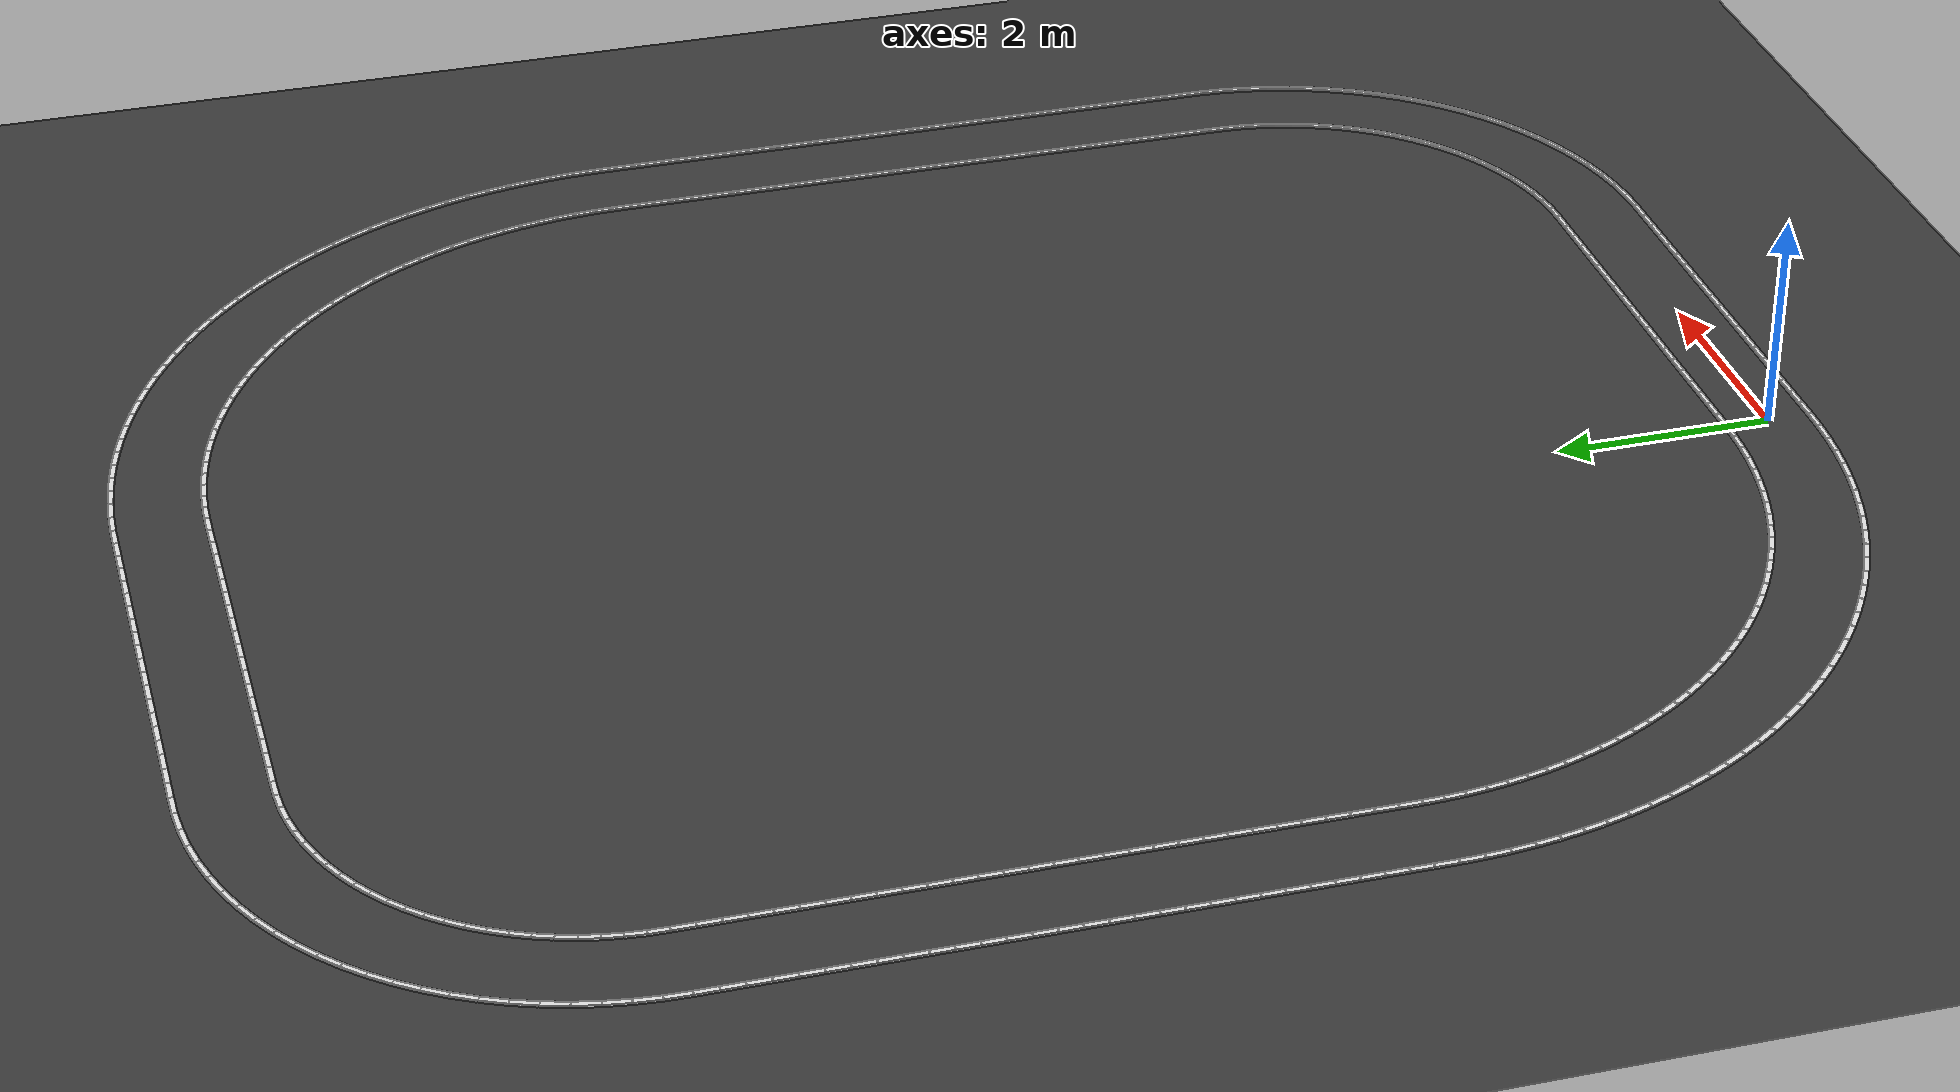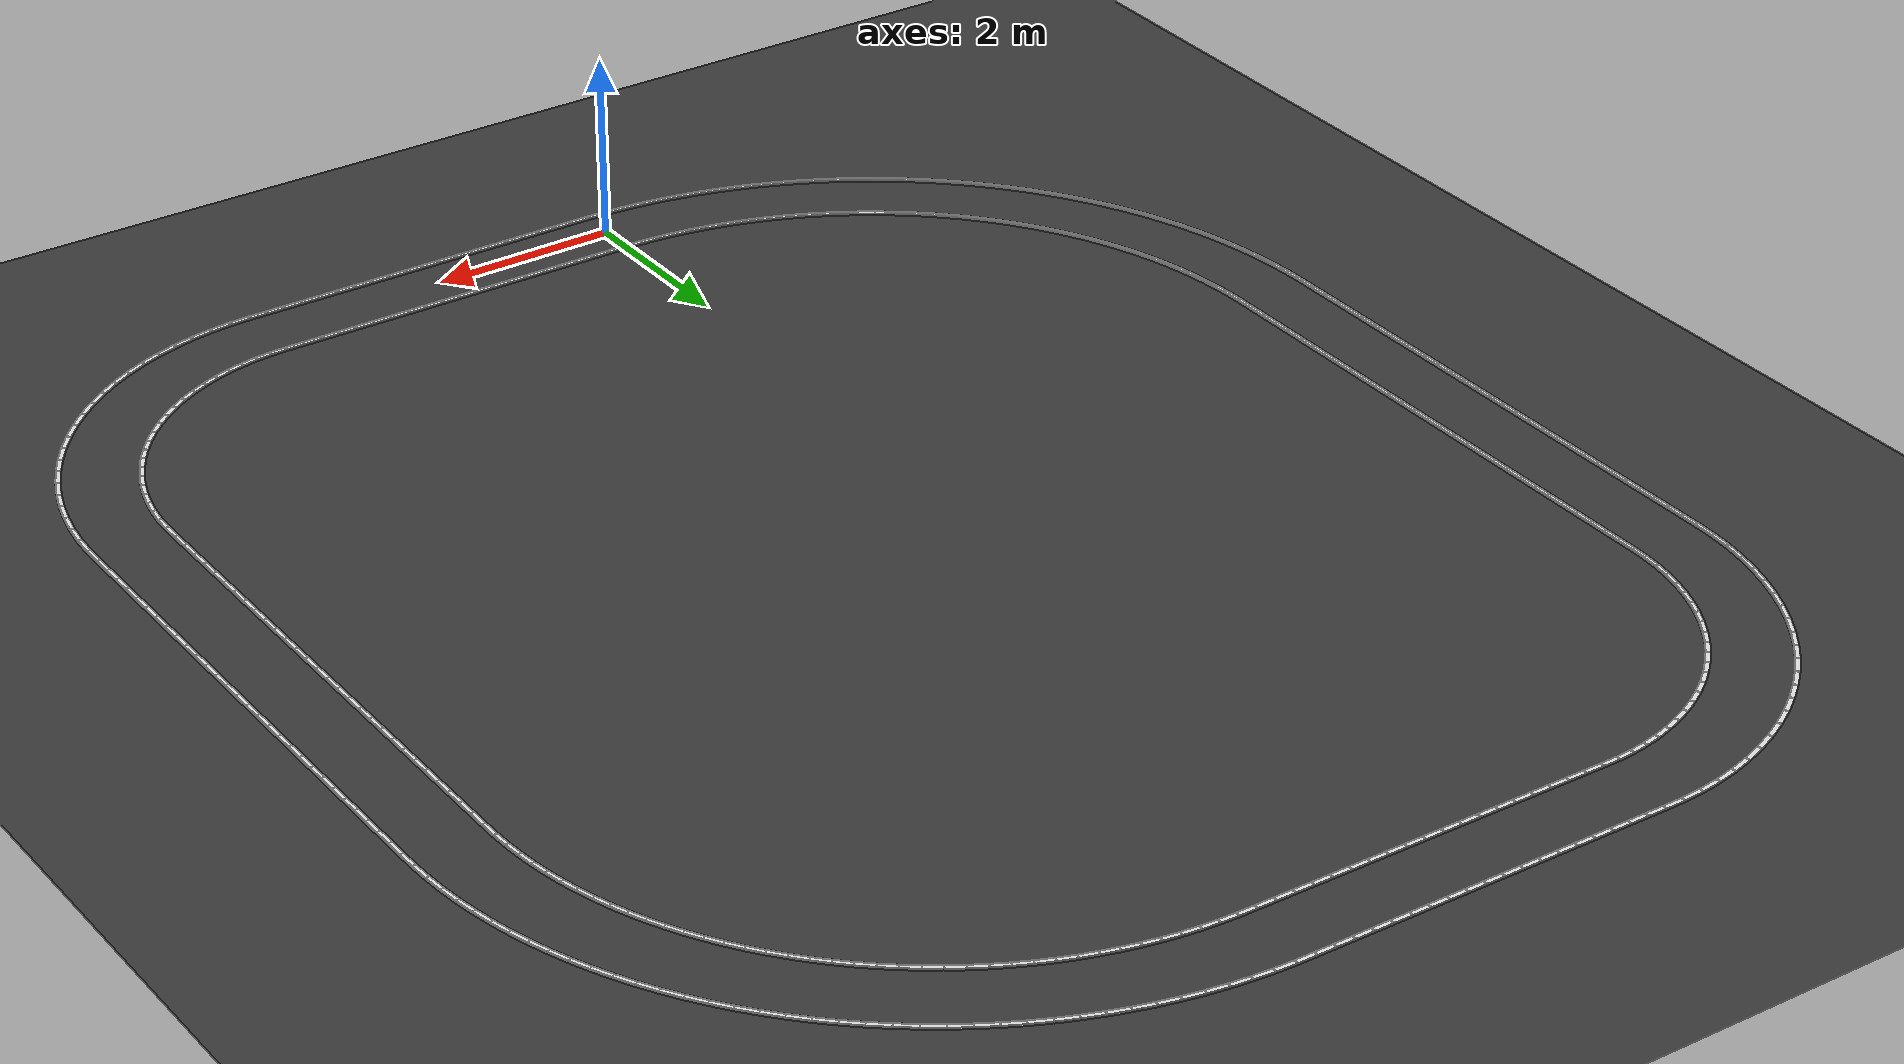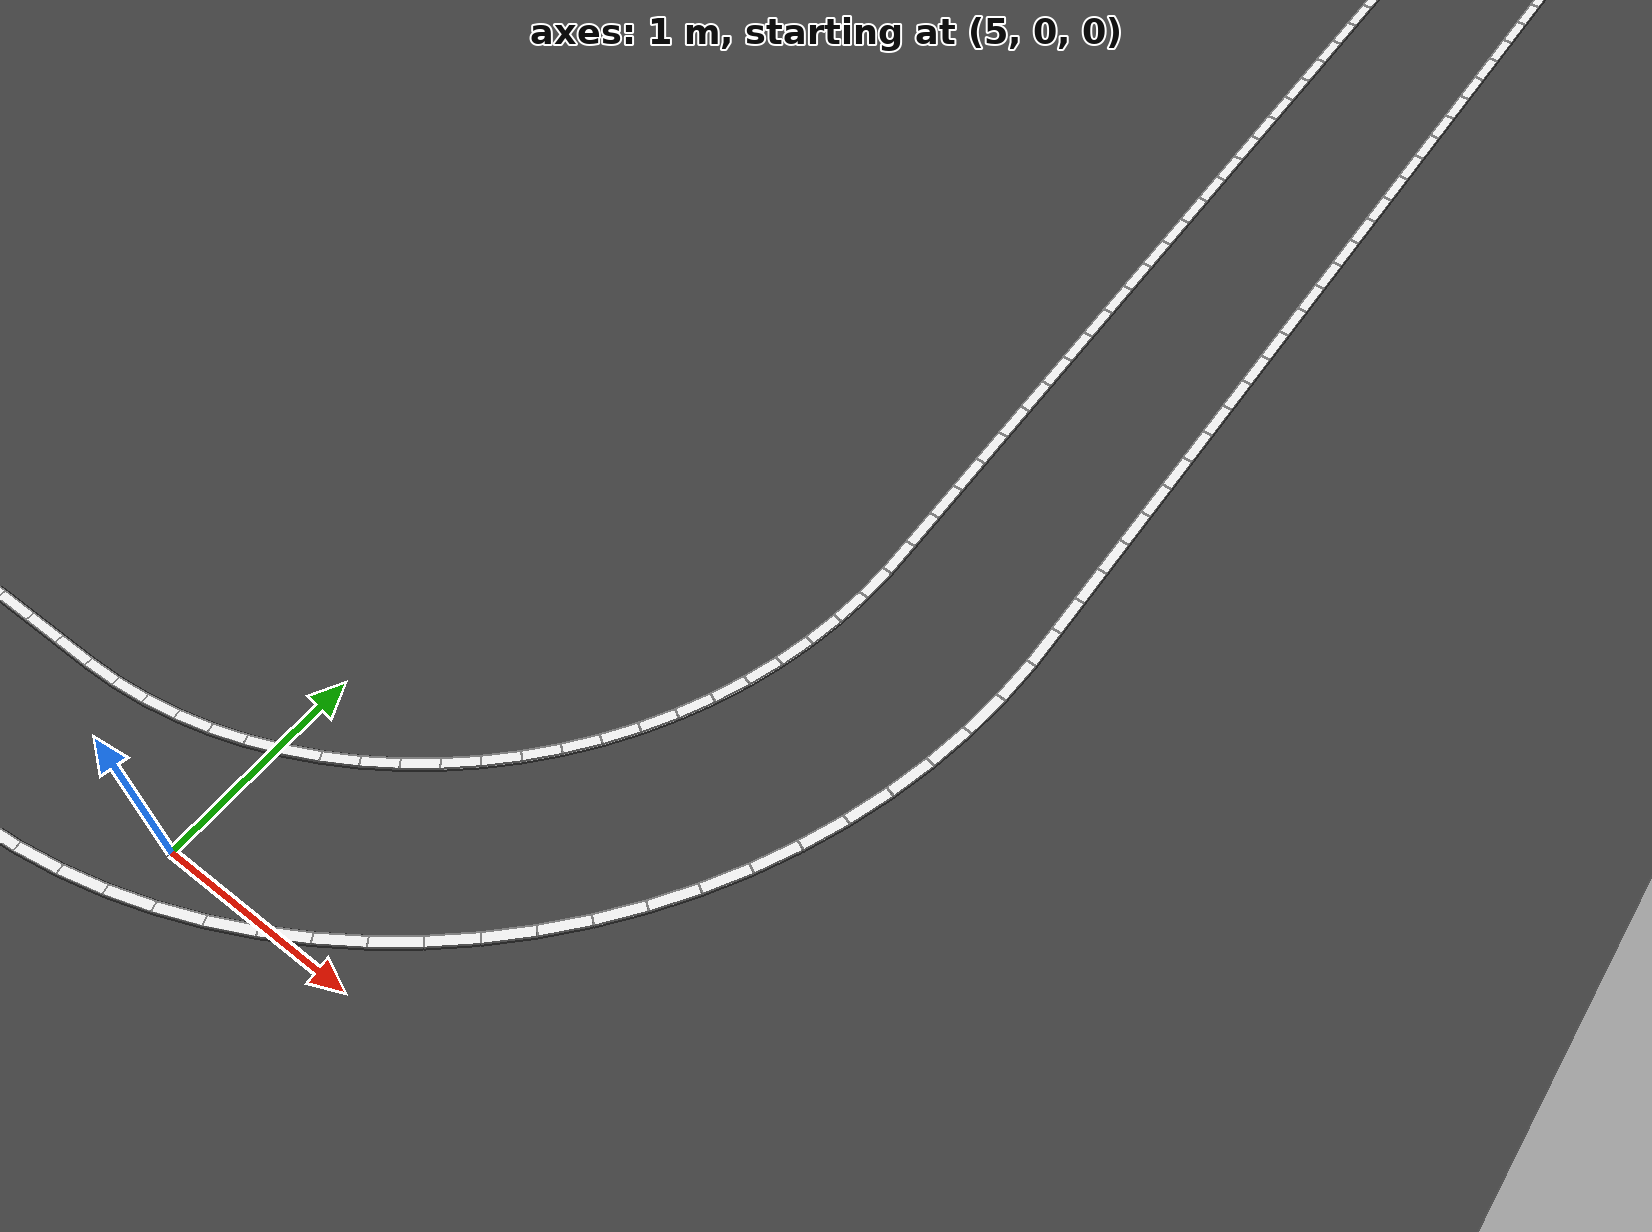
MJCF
<mujoco model="ackerman_track">
  <visual>
    <global offwidth="1280" offheight="960"/>
  </visual>
  <worldbody>
    <geom name="road_surface" type="plane" pos="1.000 7.000 0"
          size="9.000 10.000 0.01" rgba="0.25 0.25 0.25 1"/>
    <geom name="lane_left_0" type="box" pos="0.1003 0.4000 0.0100" quat="1.000000 0 0 0.000000" size="0.1003 0.0250 0.0100" rgba="0.95 0.95 0.95 1" contype="0" conaffinity="0"/>
    <geom name="lane_left_1" type="box" pos="0.3009 0.4000 0.0100" quat="1.000000 0 0 0.000000" size="0.1003 0.0250 0.0100" rgba="0.95 0.95 0.95 1" contype="0" conaffinity="0"/>
    <geom name="lane_left_2" type="box" pos="0.5015 0.4000 0.0100" quat="1.000000 0 0 0.000000" size="0.1003 0.0250 0.0100" rgba="0.95 0.95 0.95 1" contype="0" conaffinity="0"/>
    <geom name="lane_left_3" type="box" pos="0.7021 0.4000 0.0100" quat="1.000000 0 0 0.000000" size="0.1003 0.0250 0.0100" rgba="0.95 0.95 0.95 1" contype="0" conaffinity="0"/>
    <geom name="lane_left_4" type="box" pos="0.9027 0.4000 0.0100" quat="1.000000 0 0 0.000000" size="0.1003 0.0250 0.0100" rgba="0.95 0.95 0.95 1" contype="0" conaffinity="0"/>
    <geom name="lane_left_5" type="box" pos="1.1032 0.4000 0.0100" quat="1.000000 0 0 0.000000" size="0.1003 0.0250 0.0100" rgba="0.95 0.95 0.95 1" contype="0" conaffinity="0"/>
    <geom name="lane_left_6" type="box" pos="1.3038 0.4000 0.0100" quat="1.000000 0 0 0.000000" size="0.1003 0.0250 0.0100" rgba="0.95 0.95 0.95 1" contype="0" conaffinity="0"/>
    <geom name="lane_left_7" type="box" pos="1.5044 0.4000 0.0100" quat="1.000000 0 0 0.000000" size="0.1003 0.0250 0.0100" rgba="0.95 0.95 0.95 1" contype="0" conaffinity="0"/>
    <geom name="lane_left_8" type="box" pos="1.7050 0.4000 0.0100" quat="1.000000 0 0 0.000000" size="0.1003 0.0250 0.0100" rgba="0.95 0.95 0.95 1" contype="0" conaffinity="0"/>
    <geom name="lane_left_9" type="box" pos="1.9056 0.4000 0.0100" quat="1.000000 0 0 0.000000" size="0.1003 0.0250 0.0100" rgba="0.95 0.95 0.95 1" contype="0" conaffinity="0"/>
    <geom name="lane_left_10" type="box" pos="2.1062 0.4000 0.0100" quat="1.000000 0 0 0.000000" size="0.1003 0.0250 0.0100" rgba="0.95 0.95 0.95 1" contype="0" conaffinity="0"/>
    <geom name="lane_left_11" type="box" pos="2.3068 0.4000 0.0100" quat="1.000000 0 0 0.000000" size="0.1003 0.0250 0.0100" rgba="0.95 0.95 0.95 1" contype="0" conaffinity="0"/>
    <geom name="lane_left_12" type="box" pos="2.5074 0.4000 0.0100" quat="1.000000 0 0 0.000000" size="0.1003 0.0250 0.0100" rgba="0.95 0.95 0.95 1" contype="0" conaffinity="0"/>
    <geom name="lane_left_13" type="box" pos="2.7080 0.4000 0.0100" quat="1.000000 0 0 0.000000" size="0.1003 0.0250 0.0100" rgba="0.95 0.95 0.95 1" contype="0" conaffinity="0"/>
    <geom name="lane_left_14" type="box" pos="2.9086 0.4000 0.0100" quat="1.000000 0 0 0.000000" size="0.1003 0.0250 0.0100" rgba="0.95 0.95 0.95 1" contype="0" conaffinity="0"/>
    <geom name="lane_left_15" type="box" pos="3.1091 0.4000 0.0100" quat="1.000000 0 0 0.000000" size="0.1003 0.0250 0.0100" rgba="0.95 0.95 0.95 1" contype="0" conaffinity="0"/>
    <geom name="lane_left_16" type="box" pos="3.3097 0.4000 0.0100" quat="1.000000 0 0 0.000000" size="0.1003 0.0250 0.0100" rgba="0.95 0.95 0.95 1" contype="0" conaffinity="0"/>
    <geom name="lane_left_17" type="box" pos="3.5103 0.4000 0.0100" quat="1.000000 0 0 0.000000" size="0.1003 0.0250 0.0100" rgba="0.95 0.95 0.95 1" contype="0" conaffinity="0"/>
    <geom name="lane_left_18" type="box" pos="3.7109 0.4000 0.0100" quat="1.000000 0 0 0.000000" size="0.1003 0.0250 0.0100" rgba="0.95 0.95 0.95 1" contype="0" conaffinity="0"/>
    <geom name="lane_left_19" type="box" pos="3.9107 0.4000 0.0100" quat="1.000000 0 0 0.000051" size="0.0995 0.0250 0.0100" rgba="0.95 0.95 0.95 1" contype="0" conaffinity="0"/>
    <geom name="lane_left_20" type="box" pos="4.0971 0.4033 0.0100" quat="0.999825 0 0 0.018681" size="0.0869 0.0250 0.0100" rgba="0.95 0.95 0.95 1" contype="0" conaffinity="0"/>
    <geom name="lane_left_21" type="box" pos="4.2704 0.4156 0.0100" quat="0.998642 0 0 0.052090" size="0.0869 0.0250 0.0100" rgba="0.95 0.95 0.95 1" contype="0" conaffinity="0"/>
    <geom name="lane_left_22" type="box" pos="4.4424 0.4394 0.0100" quat="0.996343 0 0 0.085441" size="0.0869 0.0250 0.0100" rgba="0.95 0.95 0.95 1" contype="0" conaffinity="0"/>
    <geom name="lane_left_23" type="box" pos="4.6125 0.4747 0.0100" quat="0.992931 0 0 0.118697" size="0.0869 0.0250 0.0100" rgba="0.95 0.95 0.95 1" contype="0" conaffinity="0"/>
    <geom name="lane_left_24" type="box" pos="4.7799 0.5212 0.0100" quat="0.988408 0 0 0.151820" size="0.0869 0.0250 0.0100" rgba="0.95 0.95 0.95 1" contype="0" conaffinity="0"/>
    <geom name="lane_left_25" type="box" pos="4.9437 0.5789 0.0100" quat="0.982781 0 0 0.184773" size="0.0869 0.0250 0.0100" rgba="0.95 0.95 0.95 1" contype="0" conaffinity="0"/>
    <geom name="lane_left_26" type="box" pos="5.1034 0.6474 0.0100" quat="0.976056 0 0 0.217519" size="0.0869 0.0250 0.0100" rgba="0.95 0.95 0.95 1" contype="0" conaffinity="0"/>
    <geom name="lane_left_27" type="box" pos="5.2581 0.7263 0.0100" quat="0.968240 0 0 0.250023" size="0.0869 0.0250 0.0100" rgba="0.95 0.95 0.95 1" contype="0" conaffinity="0"/>
    <geom name="lane_left_28" type="box" pos="5.4072 0.8155 0.0100" quat="0.959342 0 0 0.282247" size="0.0869 0.0250 0.0100" rgba="0.95 0.95 0.95 1" contype="0" conaffinity="0"/>
    <geom name="lane_left_29" type="box" pos="5.5500 0.9144 0.0100" quat="0.949371 0 0 0.314156" size="0.0869 0.0250 0.0100" rgba="0.95 0.95 0.95 1" contype="0" conaffinity="0"/>
    <geom name="lane_left_30" type="box" pos="5.6859 1.0226 0.0100" quat="0.938340 0 0 0.345713" size="0.0869 0.0250 0.0100" rgba="0.95 0.95 0.95 1" contype="0" conaffinity="0"/>
    <geom name="lane_left_31" type="box" pos="5.8143 1.1397 0.0100" quat="0.926260 0 0 0.376885" size="0.0869 0.0250 0.0100" rgba="0.95 0.95 0.95 1" contype="0" conaffinity="0"/>
    <geom name="lane_left_32" type="box" pos="5.9345 1.2650 0.0100" quat="0.913145 0 0 0.407635" size="0.0869 0.0250 0.0100" rgba="0.95 0.95 0.95 1" contype="0" conaffinity="0"/>
    <geom name="lane_left_33" type="box" pos="6.0461 1.3982 0.0100" quat="0.899009 0 0 0.437929" size="0.0869 0.0250 0.0100" rgba="0.95 0.95 0.95 1" contype="0" conaffinity="0"/>
    <geom name="lane_left_34" type="box" pos="6.1486 1.5384 0.0100" quat="0.883869 0 0 0.467734" size="0.0869 0.0250 0.0100" rgba="0.95 0.95 0.95 1" contype="0" conaffinity="0"/>
    <geom name="lane_left_35" type="box" pos="6.2414 1.6853 0.0100" quat="0.867741 0 0 0.497017" size="0.0869 0.0250 0.0100" rgba="0.95 0.95 0.95 1" contype="0" conaffinity="0"/>
    <geom name="lane_left_36" type="box" pos="6.3242 1.8380 0.0100" quat="0.850643 0 0 0.525744" size="0.0869 0.0250 0.0100" rgba="0.95 0.95 0.95 1" contype="0" conaffinity="0"/>
    <geom name="lane_left_37" type="box" pos="6.3967 1.9958 0.0100" quat="0.832595 0 0 0.553883" size="0.0869 0.0250 0.0100" rgba="0.95 0.95 0.95 1" contype="0" conaffinity="0"/>
    <geom name="lane_left_38" type="box" pos="6.4584 2.1582 0.0100" quat="0.813616 0 0 0.581403" size="0.0869 0.0250 0.0100" rgba="0.95 0.95 0.95 1" contype="0" conaffinity="0"/>
    <geom name="lane_left_39" type="box" pos="6.5092 2.3244 0.0100" quat="0.793727 0 0 0.608274" size="0.0869 0.0250 0.0100" rgba="0.95 0.95 0.95 1" contype="0" conaffinity="0"/>
    <geom name="lane_left_40" type="box" pos="6.5487 2.4935 0.0100" quat="0.772952 0 0 0.634465" size="0.0869 0.0250 0.0100" rgba="0.95 0.95 0.95 1" contype="0" conaffinity="0"/>
    <geom name="lane_left_41" type="box" pos="6.5769 2.6649 0.0100" quat="0.751313 0 0 0.659946" size="0.0869 0.0250 0.0100" rgba="0.95 0.95 0.95 1" contype="0" conaffinity="0"/>
    <geom name="lane_left_42" type="box" pos="6.5935 2.8379 0.0100" quat="0.728834 0 0 0.684690" size="0.0869 0.0250 0.0100" rgba="0.95 0.95 0.95 1" contype="0" conaffinity="0"/>
    <geom name="lane_left_43" type="box" pos="6.5995 3.0191 0.0100" quat="0.709150 0 0 0.705058" size="0.0945 0.0250 0.0100" rgba="0.95 0.95 0.95 1" contype="0" conaffinity="0"/>
    <geom name="lane_left_44" type="box" pos="6.6000 3.2139 0.0100" quat="0.707107 0 0 0.707107" size="0.1003 0.0250 0.0100" rgba="0.95 0.95 0.95 1" contype="0" conaffinity="0"/>
    <geom name="lane_left_45" type="box" pos="6.6000 3.4145 0.0100" quat="0.707107 0 0 0.707107" size="0.1003 0.0250 0.0100" rgba="0.95 0.95 0.95 1" contype="0" conaffinity="0"/>
    <geom name="lane_left_46" type="box" pos="6.6000 3.6150 0.0100" quat="0.707107 0 0 0.707107" size="0.1003 0.0250 0.0100" rgba="0.95 0.95 0.95 1" contype="0" conaffinity="0"/>
    <geom name="lane_left_47" type="box" pos="6.6000 3.8156 0.0100" quat="0.707107 0 0 0.707107" size="0.1003 0.0250 0.0100" rgba="0.95 0.95 0.95 1" contype="0" conaffinity="0"/>
    <geom name="lane_left_48" type="box" pos="6.6000 4.0162 0.0100" quat="0.707107 0 0 0.707107" size="0.1003 0.0250 0.0100" rgba="0.95 0.95 0.95 1" contype="0" conaffinity="0"/>
    <geom name="lane_left_49" type="box" pos="6.6000 4.2168 0.0100" quat="0.707107 0 0 0.707107" size="0.1003 0.0250 0.0100" rgba="0.95 0.95 0.95 1" contype="0" conaffinity="0"/>
    <geom name="lane_left_50" type="box" pos="6.6000 4.4174 0.0100" quat="0.707107 0 0 0.707107" size="0.1003 0.0250 0.0100" rgba="0.95 0.95 0.95 1" contype="0" conaffinity="0"/>
    <geom name="lane_left_51" type="box" pos="6.6000 4.6180 0.0100" quat="0.707107 0 0 0.707107" size="0.1003 0.0250 0.0100" rgba="0.95 0.95 0.95 1" contype="0" conaffinity="0"/>
    <geom name="lane_left_52" type="box" pos="6.6000 4.8186 0.0100" quat="0.707107 0 0 0.707107" size="0.1003 0.0250 0.0100" rgba="0.95 0.95 0.95 1" contype="0" conaffinity="0"/>
    <geom name="lane_left_53" type="box" pos="6.6000 5.0192 0.0100" quat="0.707107 0 0 0.707107" size="0.1003 0.0250 0.0100" rgba="0.95 0.95 0.95 1" contype="0" conaffinity="0"/>
    <geom name="lane_left_54" type="box" pos="6.6000 5.2198 0.0100" quat="0.707107 0 0 0.707107" size="0.1003 0.0250 0.0100" rgba="0.95 0.95 0.95 1" contype="0" conaffinity="0"/>
    <geom name="lane_left_55" type="box" pos="6.6000 5.4204 0.0100" quat="0.707107 0 0 0.707107" size="0.1003 0.0250 0.0100" rgba="0.95 0.95 0.95 1" contype="0" conaffinity="0"/>
    <geom name="lane_left_56" type="box" pos="6.6000 5.6209 0.0100" quat="0.707107 0 0 0.707107" size="0.1003 0.0250 0.0100" rgba="0.95 0.95 0.95 1" contype="0" conaffinity="0"/>
    <geom name="lane_left_57" type="box" pos="6.6000 5.8215 0.0100" quat="0.707107 0 0 0.707107" size="0.1003 0.0250 0.0100" rgba="0.95 0.95 0.95 1" contype="0" conaffinity="0"/>
    <geom name="lane_left_58" type="box" pos="6.6000 6.0221 0.0100" quat="0.707107 0 0 0.707107" size="0.1003 0.0250 0.0100" rgba="0.95 0.95 0.95 1" contype="0" conaffinity="0"/>
    <geom name="lane_left_59" type="box" pos="6.6000 6.2227 0.0100" quat="0.707107 0 0 0.707107" size="0.1003 0.0250 0.0100" rgba="0.95 0.95 0.95 1" contype="0" conaffinity="0"/>
    <geom name="lane_left_60" type="box" pos="6.6000 6.4233 0.0100" quat="0.707107 0 0 0.707107" size="0.1003 0.0250 0.0100" rgba="0.95 0.95 0.95 1" contype="0" conaffinity="0"/>
    <geom name="lane_left_61" type="box" pos="6.6000 6.6239 0.0100" quat="0.707107 0 0 0.707107" size="0.1003 0.0250 0.0100" rgba="0.95 0.95 0.95 1" contype="0" conaffinity="0"/>
    <geom name="lane_left_62" type="box" pos="6.6000 6.8245 0.0100" quat="0.707107 0 0 0.707107" size="0.1003 0.0250 0.0100" rgba="0.95 0.95 0.95 1" contype="0" conaffinity="0"/>
    <geom name="lane_left_63" type="box" pos="6.6000 7.0251 0.0100" quat="0.707107 0 0 0.707107" size="0.1003 0.0250 0.0100" rgba="0.95 0.95 0.95 1" contype="0" conaffinity="0"/>
    <geom name="lane_left_64" type="box" pos="6.6000 7.2257 0.0100" quat="0.707107 0 0 0.707107" size="0.1003 0.0250 0.0100" rgba="0.95 0.95 0.95 1" contype="0" conaffinity="0"/>
    <geom name="lane_left_65" type="box" pos="6.6000 7.4263 0.0100" quat="0.707107 0 0 0.707107" size="0.1003 0.0250 0.0100" rgba="0.95 0.95 0.95 1" contype="0" conaffinity="0"/>
    <geom name="lane_left_66" type="box" pos="6.6000 7.6268 0.0100" quat="0.707107 0 0 0.707107" size="0.1003 0.0250 0.0100" rgba="0.95 0.95 0.95 1" contype="0" conaffinity="0"/>
    <geom name="lane_left_67" type="box" pos="6.6000 7.8274 0.0100" quat="0.707107 0 0 0.707107" size="0.1003 0.0250 0.0100" rgba="0.95 0.95 0.95 1" contype="0" conaffinity="0"/>
    <geom name="lane_left_68" type="box" pos="6.6000 8.0280 0.0100" quat="0.707107 0 0 0.707107" size="0.1003 0.0250 0.0100" rgba="0.95 0.95 0.95 1" contype="0" conaffinity="0"/>
    <geom name="lane_left_69" type="box" pos="6.6000 8.2286 0.0100" quat="0.707107 0 0 0.707107" size="0.1003 0.0250 0.0100" rgba="0.95 0.95 0.95 1" contype="0" conaffinity="0"/>
    <geom name="lane_left_70" type="box" pos="6.6000 8.4292 0.0100" quat="0.707107 0 0 0.707107" size="0.1003 0.0250 0.0100" rgba="0.95 0.95 0.95 1" contype="0" conaffinity="0"/>
    <geom name="lane_left_71" type="box" pos="6.6000 8.6298 0.0100" quat="0.707107 0 0 0.707107" size="0.1003 0.0250 0.0100" rgba="0.95 0.95 0.95 1" contype="0" conaffinity="0"/>
    <geom name="lane_left_72" type="box" pos="6.6000 8.8304 0.0100" quat="0.707107 0 0 0.707107" size="0.1003 0.0250 0.0100" rgba="0.95 0.95 0.95 1" contype="0" conaffinity="0"/>
    <geom name="lane_left_73" type="box" pos="6.5992 9.0257 0.0100" quat="0.704152 0 0 0.710049" size="0.0950 0.0250 0.0100" rgba="0.95 0.95 0.95 1" contype="0" conaffinity="0"/>
    <geom name="lane_left_74" type="box" pos="6.5941 9.2129 0.0100" quat="0.690545 0 0 0.723290" size="0.0923 0.0250 0.0100" rgba="0.95 0.95 0.95 1" contype="0" conaffinity="0"/>
    <geom name="lane_left_75" type="box" pos="6.5819 9.3970 0.0100" quat="0.675898 0 0 0.736995" size="0.0923 0.0250 0.0100" rgba="0.95 0.95 0.95 1" contype="0" conaffinity="0"/>
    <geom name="lane_left_76" type="box" pos="6.5623 9.5805 0.0100" quat="0.660980 0 0 0.750404" size="0.0923 0.0250 0.0100" rgba="0.95 0.95 0.95 1" contype="0" conaffinity="0"/>
    <geom name="lane_left_77" type="box" pos="6.5353 9.7630 0.0100" quat="0.645796 0 0 0.763510" size="0.0923 0.0250 0.0100" rgba="0.95 0.95 0.95 1" contype="0" conaffinity="0"/>
    <geom name="lane_left_78" type="box" pos="6.5011 9.9443 0.0100" quat="0.630351 0 0 0.776310" size="0.0923 0.0250 0.0100" rgba="0.95 0.95 0.95 1" contype="0" conaffinity="0"/>
    <geom name="lane_left_79" type="box" pos="6.4596 10.1240 0.0100" quat="0.614654 0 0 0.788797" size="0.0923 0.0250 0.0100" rgba="0.95 0.95 0.95 1" contype="0" conaffinity="0"/>
    <geom name="lane_left_80" type="box" pos="6.4109 10.3020 0.0100" quat="0.598709 0 0 0.800967" size="0.0923 0.0250 0.0100" rgba="0.95 0.95 0.95 1" contype="0" conaffinity="0"/>
    <geom name="lane_left_81" type="box" pos="6.3552 10.4778 0.0100" quat="0.582523 0 0 0.812814" size="0.0923 0.0250 0.0100" rgba="0.95 0.95 0.95 1" contype="0" conaffinity="0"/>
    <geom name="lane_left_82" type="box" pos="6.2924 10.6513 0.0100" quat="0.566102 0 0 0.824335" size="0.0923 0.0250 0.0100" rgba="0.95 0.95 0.95 1" contype="0" conaffinity="0"/>
    <geom name="lane_left_83" type="box" pos="6.2227 10.8222 0.0100" quat="0.549454 0 0 0.835524" size="0.0923 0.0250 0.0100" rgba="0.95 0.95 0.95 1" contype="0" conaffinity="0"/>
    <geom name="lane_left_84" type="box" pos="6.1462 10.9900 0.0100" quat="0.532585 0 0 0.846376" size="0.0923 0.0250 0.0100" rgba="0.95 0.95 0.95 1" contype="0" conaffinity="0"/>
    <geom name="lane_left_85" type="box" pos="6.0631 11.1547 0.0100" quat="0.515502 0 0 0.856889" size="0.0923 0.0250 0.0100" rgba="0.95 0.95 0.95 1" contype="0" conaffinity="0"/>
    <geom name="lane_left_86" type="box" pos="5.9734 11.3160 0.0100" quat="0.498211 0 0 0.867056" size="0.0923 0.0250 0.0100" rgba="0.95 0.95 0.95 1" contype="0" conaffinity="0"/>
    <geom name="lane_left_87" type="box" pos="5.8773 11.4735 0.0100" quat="0.480719 0 0 0.876875" size="0.0923 0.0250 0.0100" rgba="0.95 0.95 0.95 1" contype="0" conaffinity="0"/>
    <geom name="lane_left_88" type="box" pos="5.7750 11.6270 0.0100" quat="0.463035 0 0 0.886340" size="0.0923 0.0250 0.0100" rgba="0.95 0.95 0.95 1" contype="0" conaffinity="0"/>
    <geom name="lane_left_89" type="box" pos="5.6666 11.7763 0.0100" quat="0.445164 0 0 0.895449" size="0.0923 0.0250 0.0100" rgba="0.95 0.95 0.95 1" contype="0" conaffinity="0"/>
    <geom name="lane_left_90" type="box" pos="5.5523 11.9211 0.0100" quat="0.427113 0 0 0.904198" size="0.0923 0.0250 0.0100" rgba="0.95 0.95 0.95 1" contype="0" conaffinity="0"/>
    <geom name="lane_left_91" type="box" pos="5.4323 12.0612 0.0100" quat="0.408891 0 0 0.912583" size="0.0923 0.0250 0.0100" rgba="0.95 0.95 0.95 1" contype="0" conaffinity="0"/>
    <geom name="lane_left_92" type="box" pos="5.3067 12.1964 0.0100" quat="0.390505 0 0 0.920601" size="0.0923 0.0250 0.0100" rgba="0.95 0.95 0.95 1" contype="0" conaffinity="0"/>
    <geom name="lane_left_93" type="box" pos="5.1759 12.3265 0.0100" quat="0.371961 0 0 0.928248" size="0.0923 0.0250 0.0100" rgba="0.95 0.95 0.95 1" contype="0" conaffinity="0"/>
    <geom name="lane_left_94" type="box" pos="5.0399 12.4512 0.0100" quat="0.353268 0 0 0.935522" size="0.0923 0.0250 0.0100" rgba="0.95 0.95 0.95 1" contype="0" conaffinity="0"/>
    <geom name="lane_left_95" type="box" pos="4.8990 12.5703 0.0100" quat="0.334432 0 0 0.942420" size="0.0923 0.0250 0.0100" rgba="0.95 0.95 0.95 1" contype="0" conaffinity="0"/>
    <geom name="lane_left_96" type="box" pos="4.7535 12.6837 0.0100" quat="0.315462 0 0 0.948938" size="0.0923 0.0250 0.0100" rgba="0.95 0.95 0.95 1" contype="0" conaffinity="0"/>
    <geom name="lane_left_97" type="box" pos="4.6035 12.7912 0.0100" quat="0.296366 0 0 0.955075" size="0.0923 0.0250 0.0100" rgba="0.95 0.95 0.95 1" contype="0" conaffinity="0"/>
    <geom name="lane_left_98" type="box" pos="4.4494 12.8925 0.0100" quat="0.277149 0 0 0.960827" size="0.0923 0.0250 0.0100" rgba="0.95 0.95 0.95 1" contype="0" conaffinity="0"/>
    <geom name="lane_left_99" type="box" pos="4.2913 12.9877 0.0100" quat="0.257822 0 0 0.966193" size="0.0923 0.0250 0.0100" rgba="0.95 0.95 0.95 1" contype="0" conaffinity="0"/>
    <geom name="lane_left_100" type="box" pos="4.1295 13.0763 0.0100" quat="0.238390 0 0 0.971169" size="0.0923 0.0250 0.0100" rgba="0.95 0.95 0.95 1" contype="0" conaffinity="0"/>
    <geom name="lane_left_101" type="box" pos="3.9643 13.1585 0.0100" quat="0.218863 0 0 0.975756" size="0.0923 0.0250 0.0100" rgba="0.95 0.95 0.95 1" contype="0" conaffinity="0"/>
    <geom name="lane_left_102" type="box" pos="3.7960 13.2339 0.0100" quat="0.199247 0 0 0.979949" size="0.0923 0.0250 0.0100" rgba="0.95 0.95 0.95 1" contype="0" conaffinity="0"/>
    <geom name="lane_left_103" type="box" pos="3.6247 13.3025 0.0100" quat="0.179552 0 0 0.983748" size="0.0923 0.0250 0.0100" rgba="0.95 0.95 0.95 1" contype="0" conaffinity="0"/>
    <geom name="lane_left_104" type="box" pos="3.4508 13.3642 0.0100" quat="0.159784 0 0 0.987152" size="0.0923 0.0250 0.0100" rgba="0.95 0.95 0.95 1" contype="0" conaffinity="0"/>
    <geom name="lane_left_105" type="box" pos="3.2746 13.4189 0.0100" quat="0.139952 0 0 0.990158" size="0.0923 0.0250 0.0100" rgba="0.95 0.95 0.95 1" contype="0" conaffinity="0"/>
    <geom name="lane_left_106" type="box" pos="3.0964 13.4665 0.0100" quat="0.120064 0 0 0.992766" size="0.0923 0.0250 0.0100" rgba="0.95 0.95 0.95 1" contype="0" conaffinity="0"/>
    <geom name="lane_left_107" type="box" pos="2.9164 13.5069 0.0100" quat="0.100127 0 0 0.994975" size="0.0923 0.0250 0.0100" rgba="0.95 0.95 0.95 1" contype="0" conaffinity="0"/>
    <geom name="lane_left_108" type="box" pos="2.7349 13.5400 0.0100" quat="0.080150 0 0 0.996783" size="0.0923 0.0250 0.0100" rgba="0.95 0.95 0.95 1" contype="0" conaffinity="0"/>
    <geom name="lane_left_109" type="box" pos="2.5522 13.5658 0.0100" quat="0.060141 0 0 0.998190" size="0.0923 0.0250 0.0100" rgba="0.95 0.95 0.95 1" contype="0" conaffinity="0"/>
    <geom name="lane_left_110" type="box" pos="2.3686 13.5843 0.0100" quat="0.040107 0 0 0.999195" size="0.0923 0.0250 0.0100" rgba="0.95 0.95 0.95 1" contype="0" conaffinity="0"/>
    <geom name="lane_left_111" type="box" pos="2.1845 13.5954 0.0100" quat="0.020058 0 0 0.999799" size="0.0923 0.0250 0.0100" rgba="0.95 0.95 0.95 1" contype="0" conaffinity="0"/>
    <geom name="lane_left_112" type="box" pos="1.9960 13.5995 0.0100" quat="0.002403 0 0 0.999997" size="0.0963 0.0250 0.0100" rgba="0.95 0.95 0.95 1" contype="0" conaffinity="0"/>
    <geom name="lane_left_113" type="box" pos="1.7994 13.6000 0.0100" quat="0.000000 0 0 1.000000" size="0.1003 0.0250 0.0100" rgba="0.95 0.95 0.95 1" contype="0" conaffinity="0"/>
    <geom name="lane_left_114" type="box" pos="1.5988 13.6000 0.0100" quat="0.000000 0 0 1.000000" size="0.1003 0.0250 0.0100" rgba="0.95 0.95 0.95 1" contype="0" conaffinity="0"/>
    <geom name="lane_left_115" type="box" pos="1.3982 13.6000 0.0100" quat="0.000000 0 0 1.000000" size="0.1003 0.0250 0.0100" rgba="0.95 0.95 0.95 1" contype="0" conaffinity="0"/>
    <geom name="lane_left_116" type="box" pos="1.1976 13.6000 0.0100" quat="0.000000 0 0 1.000000" size="0.1003 0.0250 0.0100" rgba="0.95 0.95 0.95 1" contype="0" conaffinity="0"/>
    <geom name="lane_left_117" type="box" pos="0.9971 13.6000 0.0100" quat="0.000000 0 0 1.000000" size="0.1003 0.0250 0.0100" rgba="0.95 0.95 0.95 1" contype="0" conaffinity="0"/>
    <geom name="lane_left_118" type="box" pos="0.7965 13.6000 0.0100" quat="0.000000 0 0 1.000000" size="0.1003 0.0250 0.0100" rgba="0.95 0.95 0.95 1" contype="0" conaffinity="0"/>
    <geom name="lane_left_119" type="box" pos="0.5959 13.6000 0.0100" quat="0.000000 0 0 1.000000" size="0.1003 0.0250 0.0100" rgba="0.95 0.95 0.95 1" contype="0" conaffinity="0"/>
    <geom name="lane_left_120" type="box" pos="0.3953 13.6000 0.0100" quat="0.000000 0 0 1.000000" size="0.1003 0.0250 0.0100" rgba="0.95 0.95 0.95 1" contype="0" conaffinity="0"/>
    <geom name="lane_left_121" type="box" pos="0.1947 13.6000 0.0100" quat="0.000000 0 0 1.000000" size="0.1003 0.0250 0.0100" rgba="0.95 0.95 0.95 1" contype="0" conaffinity="0"/>
    <geom name="lane_left_122" type="box" pos="-0.0059 13.6000 0.0100" quat="0.000000 0 0 1.000000" size="0.1003 0.0250 0.0100" rgba="0.95 0.95 0.95 1" contype="0" conaffinity="0"/>
    <geom name="lane_left_123" type="box" pos="-0.2065 13.6000 0.0100" quat="0.000000 0 0 1.000000" size="0.1003 0.0250 0.0100" rgba="0.95 0.95 0.95 1" contype="0" conaffinity="0"/>
    <geom name="lane_left_124" type="box" pos="-0.4071 13.6000 0.0100" quat="0.000000 0 0 1.000000" size="0.1003 0.0250 0.0100" rgba="0.95 0.95 0.95 1" contype="0" conaffinity="0"/>
    <geom name="lane_left_125" type="box" pos="-0.6077 13.6000 0.0100" quat="0.000000 0 0 1.000000" size="0.1003 0.0250 0.0100" rgba="0.95 0.95 0.95 1" contype="0" conaffinity="0"/>
    <geom name="lane_left_126" type="box" pos="-0.8083 13.6000 0.0100" quat="0.000000 0 0 1.000000" size="0.1003 0.0250 0.0100" rgba="0.95 0.95 0.95 1" contype="0" conaffinity="0"/>
    <geom name="lane_left_127" type="box" pos="-1.0088 13.6000 0.0100" quat="0.000000 0 0 1.000000" size="0.1003 0.0250 0.0100" rgba="0.95 0.95 0.95 1" contype="0" conaffinity="0"/>
    <geom name="lane_left_128" type="box" pos="-1.2094 13.6000 0.0100" quat="0.000000 0 0 1.000000" size="0.1003 0.0250 0.0100" rgba="0.95 0.95 0.95 1" contype="0" conaffinity="0"/>
    <geom name="lane_left_129" type="box" pos="-1.4100 13.6000 0.0100" quat="0.000000 0 0 1.000000" size="0.1003 0.0250 0.0100" rgba="0.95 0.95 0.95 1" contype="0" conaffinity="0"/>
    <geom name="lane_left_130" type="box" pos="-1.6106 13.6000 0.0100" quat="0.000000 0 0 1.000000" size="0.1003 0.0250 0.0100" rgba="0.95 0.95 0.95 1" contype="0" conaffinity="0"/>
    <geom name="lane_left_131" type="box" pos="-1.8112 13.6000 0.0100" quat="0.000000 0 0 1.000000" size="0.1003 0.0250 0.0100" rgba="0.95 0.95 0.95 1" contype="0" conaffinity="0"/>
    <geom name="lane_left_132" type="box" pos="-2.0043 13.5991 0.0100" quat="0.004888 0 0 -0.999988" size="0.0928 0.0250 0.0100" rgba="0.95 0.95 0.95 1" contype="0" conaffinity="0"/>
    <geom name="lane_left_133" type="box" pos="-2.1838 13.5920 0.0100" quat="0.035391 0 0 -0.999374" size="0.0869 0.0250 0.0100" rgba="0.95 0.95 0.95 1" contype="0" conaffinity="0"/>
    <geom name="lane_left_134" type="box" pos="-2.3566 13.5740 0.0100" quat="0.068776 0 0 -0.997632" size="0.0869 0.0250 0.0100" rgba="0.95 0.95 0.95 1" contype="0" conaffinity="0"/>
    <geom name="lane_left_135" type="box" pos="-2.5278 13.5444 0.0100" quat="0.102083 0 0 -0.994776" size="0.0869 0.0250 0.0100" rgba="0.95 0.95 0.95 1" contype="0" conaffinity="0"/>
    <geom name="lane_left_136" type="box" pos="-2.6966 13.5034 0.0100" quat="0.135277 0 0 -0.990808" size="0.0869 0.0250 0.0100" rgba="0.95 0.95 0.95 1" contype="0" conaffinity="0"/>
    <geom name="lane_left_137" type="box" pos="-2.8623 13.4513 0.0100" quat="0.168320 0 0 -0.985732" size="0.0869 0.0250 0.0100" rgba="0.95 0.95 0.95 1" contype="0" conaffinity="0"/>
    <geom name="lane_left_138" type="box" pos="-3.0241 13.3882 0.0100" quat="0.201174 0 0 -0.979555" size="0.0869 0.0250 0.0100" rgba="0.95 0.95 0.95 1" contype="0" conaffinity="0"/>
    <geom name="lane_left_139" type="box" pos="-3.1814 13.3145 0.0100" quat="0.233804 0 0 -0.972284" size="0.0869 0.0250 0.0100" rgba="0.95 0.95 0.95 1" contype="0" conaffinity="0"/>
    <geom name="lane_left_140" type="box" pos="-3.3334 13.2303 0.0100" quat="0.266172 0 0 -0.963925" size="0.0869 0.0250 0.0100" rgba="0.95 0.95 0.95 1" contype="0" conaffinity="0"/>
    <geom name="lane_left_141" type="box" pos="-3.4795 13.1363 0.0100" quat="0.298243 0 0 -0.954490" size="0.0869 0.0250 0.0100" rgba="0.95 0.95 0.95 1" contype="0" conaffinity="0"/>
    <geom name="lane_left_142" type="box" pos="-3.6189 13.0326 0.0100" quat="0.329981 0 0 -0.943988" size="0.0869 0.0250 0.0100" rgba="0.95 0.95 0.95 1" contype="0" conaffinity="0"/>
    <geom name="lane_left_143" type="box" pos="-3.7511 12.9199 0.0100" quat="0.361350 0 0 -0.932430" size="0.0869 0.0250 0.0100" rgba="0.95 0.95 0.95 1" contype="0" conaffinity="0"/>
    <geom name="lane_left_144" type="box" pos="-3.8754 12.7987 0.0100" quat="0.392314 0 0 -0.919831" size="0.0869 0.0250 0.0100" rgba="0.95 0.95 0.95 1" contype="0" conaffinity="0"/>
    <geom name="lane_left_145" type="box" pos="-3.9914 12.6693 0.0100" quat="0.422841 0 0 -0.906204" size="0.0869 0.0250 0.0100" rgba="0.95 0.95 0.95 1" contype="0" conaffinity="0"/>
    <geom name="lane_left_146" type="box" pos="-4.0985 12.5326 0.0100" quat="0.452895 0 0 -0.891564" size="0.0869 0.0250 0.0100" rgba="0.95 0.95 0.95 1" contype="0" conaffinity="0"/>
    <geom name="lane_left_147" type="box" pos="-4.1962 12.3889 0.0100" quat="0.482443 0 0 -0.875927" size="0.0869 0.0250 0.0100" rgba="0.95 0.95 0.95 1" contype="0" conaffinity="0"/>
    <geom name="lane_left_148" type="box" pos="-4.2841 12.2391 0.0100" quat="0.511452 0 0 -0.859312" size="0.0869 0.0250 0.0100" rgba="0.95 0.95 0.95 1" contype="0" conaffinity="0"/>
    <geom name="lane_left_149" type="box" pos="-4.3618 12.0837 0.0100" quat="0.539889 0 0 -0.841736" size="0.0869 0.0250 0.0100" rgba="0.95 0.95 0.95 1" contype="0" conaffinity="0"/>
    <geom name="lane_left_150" type="box" pos="-4.4289 11.9235 0.0100" quat="0.567722 0 0 -0.823220" size="0.0869 0.0250 0.0100" rgba="0.95 0.95 0.95 1" contype="0" conaffinity="0"/>
    <geom name="lane_left_151" type="box" pos="-4.4852 11.7591 0.0100" quat="0.594922 0 0 -0.803784" size="0.0869 0.0250 0.0100" rgba="0.95 0.95 0.95 1" contype="0" conaffinity="0"/>
    <geom name="lane_left_152" type="box" pos="-4.5304 11.5914 0.0100" quat="0.621456 0 0 -0.783449" size="0.0869 0.0250 0.0100" rgba="0.95 0.95 0.95 1" contype="0" conaffinity="0"/>
    <geom name="lane_left_153" type="box" pos="-4.5642 11.4210 0.0100" quat="0.647296 0 0 -0.762239" size="0.0869 0.0250 0.0100" rgba="0.95 0.95 0.95 1" contype="0" conaffinity="0"/>
    <geom name="lane_left_154" type="box" pos="-4.5866 11.2487 0.0100" quat="0.672412 0 0 -0.740177" size="0.0869 0.0250 0.0100" rgba="0.95 0.95 0.95 1" contype="0" conaffinity="0"/>
    <geom name="lane_left_155" type="box" pos="-4.5975 11.0745 0.0100" quat="0.696830 0 0 -0.717236" size="0.0878 0.0250 0.0100" rgba="0.95 0.95 0.95 1" contype="0" conaffinity="0"/>
    <geom name="lane_left_156" type="box" pos="-4.6000 10.8864 0.0100" quat="0.707107 0 0 -0.707107" size="0.1003 0.0250 0.0100" rgba="0.95 0.95 0.95 1" contype="0" conaffinity="0"/>
    <geom name="lane_left_157" type="box" pos="-4.6000 10.6858 0.0100" quat="0.707107 0 0 -0.707107" size="0.1003 0.0250 0.0100" rgba="0.95 0.95 0.95 1" contype="0" conaffinity="0"/>
    <geom name="lane_left_158" type="box" pos="-4.6000 10.4853 0.0100" quat="0.707107 0 0 -0.707107" size="0.1003 0.0250 0.0100" rgba="0.95 0.95 0.95 1" contype="0" conaffinity="0"/>
    <geom name="lane_left_159" type="box" pos="-4.6000 10.2847 0.0100" quat="0.707107 0 0 -0.707107" size="0.1003 0.0250 0.0100" rgba="0.95 0.95 0.95 1" contype="0" conaffinity="0"/>
    <geom name="lane_left_160" type="box" pos="-4.6000 10.0841 0.0100" quat="0.707107 0 0 -0.707107" size="0.1003 0.0250 0.0100" rgba="0.95 0.95 0.95 1" contype="0" conaffinity="0"/>
    <geom name="lane_left_161" type="box" pos="-4.6000 9.8835 0.0100" quat="0.707107 0 0 -0.707107" size="0.1003 0.0250 0.0100" rgba="0.95 0.95 0.95 1" contype="0" conaffinity="0"/>
    <geom name="lane_left_162" type="box" pos="-4.6000 9.6829 0.0100" quat="0.707107 0 0 -0.707107" size="0.1003 0.0250 0.0100" rgba="0.95 0.95 0.95 1" contype="0" conaffinity="0"/>
    <geom name="lane_left_163" type="box" pos="-4.6000 9.4823 0.0100" quat="0.707107 0 0 -0.707107" size="0.1003 0.0250 0.0100" rgba="0.95 0.95 0.95 1" contype="0" conaffinity="0"/>
    <geom name="lane_left_164" type="box" pos="-4.6000 9.2817 0.0100" quat="0.707107 0 0 -0.707107" size="0.1003 0.0250 0.0100" rgba="0.95 0.95 0.95 1" contype="0" conaffinity="0"/>
    <geom name="lane_left_165" type="box" pos="-4.6000 9.0811 0.0100" quat="0.707107 0 0 -0.707107" size="0.1003 0.0250 0.0100" rgba="0.95 0.95 0.95 1" contype="0" conaffinity="0"/>
    <geom name="lane_left_166" type="box" pos="-4.6000 8.8805 0.0100" quat="0.707107 0 0 -0.707107" size="0.1003 0.0250 0.0100" rgba="0.95 0.95 0.95 1" contype="0" conaffinity="0"/>
    <geom name="lane_left_167" type="box" pos="-4.6000 8.6799 0.0100" quat="0.707107 0 0 -0.707107" size="0.1003 0.0250 0.0100" rgba="0.95 0.95 0.95 1" contype="0" conaffinity="0"/>
    <geom name="lane_left_168" type="box" pos="-4.6000 8.4794 0.0100" quat="0.707107 0 0 -0.707107" size="0.1003 0.0250 0.0100" rgba="0.95 0.95 0.95 1" contype="0" conaffinity="0"/>
    <geom name="lane_left_169" type="box" pos="-4.6000 8.2788 0.0100" quat="0.707107 0 0 -0.707107" size="0.1003 0.0250 0.0100" rgba="0.95 0.95 0.95 1" contype="0" conaffinity="0"/>
    <geom name="lane_left_170" type="box" pos="-4.6000 8.0782 0.0100" quat="0.707107 0 0 -0.707107" size="0.1003 0.0250 0.0100" rgba="0.95 0.95 0.95 1" contype="0" conaffinity="0"/>
    <geom name="lane_left_171" type="box" pos="-4.6000 7.8776 0.0100" quat="0.707107 0 0 -0.707107" size="0.1003 0.0250 0.0100" rgba="0.95 0.95 0.95 1" contype="0" conaffinity="0"/>
    <geom name="lane_left_172" type="box" pos="-4.6000 7.6770 0.0100" quat="0.707107 0 0 -0.707107" size="0.1003 0.0250 0.0100" rgba="0.95 0.95 0.95 1" contype="0" conaffinity="0"/>
    <geom name="lane_left_173" type="box" pos="-4.6000 7.4764 0.0100" quat="0.707107 0 0 -0.707107" size="0.1003 0.0250 0.0100" rgba="0.95 0.95 0.95 1" contype="0" conaffinity="0"/>
    <geom name="lane_left_174" type="box" pos="-4.6000 7.2758 0.0100" quat="0.707107 0 0 -0.707107" size="0.1003 0.0250 0.0100" rgba="0.95 0.95 0.95 1" contype="0" conaffinity="0"/>
    <geom name="lane_left_175" type="box" pos="-4.6000 7.0752 0.0100" quat="0.707107 0 0 -0.707107" size="0.1003 0.0250 0.0100" rgba="0.95 0.95 0.95 1" contype="0" conaffinity="0"/>
    <geom name="lane_left_176" type="box" pos="-4.6000 6.8746 0.0100" quat="0.707107 0 0 -0.707107" size="0.1003 0.0250 0.0100" rgba="0.95 0.95 0.95 1" contype="0" conaffinity="0"/>
    <geom name="lane_left_177" type="box" pos="-4.6000 6.6740 0.0100" quat="0.707107 0 0 -0.707107" size="0.1003 0.0250 0.0100" rgba="0.95 0.95 0.95 1" contype="0" conaffinity="0"/>
    <geom name="lane_left_178" type="box" pos="-4.6000 6.4735 0.0100" quat="0.707107 0 0 -0.707107" size="0.1003 0.0250 0.0100" rgba="0.95 0.95 0.95 1" contype="0" conaffinity="0"/>
    <geom name="lane_left_179" type="box" pos="-4.6000 6.2729 0.0100" quat="0.707107 0 0 -0.707107" size="0.1003 0.0250 0.0100" rgba="0.95 0.95 0.95 1" contype="0" conaffinity="0"/>
    <geom name="lane_left_180" type="box" pos="-4.6000 6.0723 0.0100" quat="0.707107 0 0 -0.707107" size="0.1003 0.0250 0.0100" rgba="0.95 0.95 0.95 1" contype="0" conaffinity="0"/>
    <geom name="lane_left_181" type="box" pos="-4.6000 5.8717 0.0100" quat="0.707107 0 0 -0.707107" size="0.1003 0.0250 0.0100" rgba="0.95 0.95 0.95 1" contype="0" conaffinity="0"/>
    <geom name="lane_left_182" type="box" pos="-4.6000 5.6711 0.0100" quat="0.707107 0 0 -0.707107" size="0.1003 0.0250 0.0100" rgba="0.95 0.95 0.95 1" contype="0" conaffinity="0"/>
    <geom name="lane_left_183" type="box" pos="-4.6000 5.4705 0.0100" quat="0.707107 0 0 -0.707107" size="0.1003 0.0250 0.0100" rgba="0.95 0.95 0.95 1" contype="0" conaffinity="0"/>
    <geom name="lane_left_184" type="box" pos="-4.6000 5.2699 0.0100" quat="0.707107 0 0 -0.707107" size="0.1003 0.0250 0.0100" rgba="0.95 0.95 0.95 1" contype="0" conaffinity="0"/>
    <geom name="lane_left_185" type="box" pos="-4.6000 5.0706 0.0100" quat="0.707264 0 0 -0.706949" size="0.0991 0.0250 0.0100" rgba="0.95 0.95 0.95 1" contype="0" conaffinity="0"/>
    <geom name="lane_left_186" type="box" pos="-4.5975 4.8793 0.0100" quat="0.716328 0 0 -0.697764" size="0.0923 0.0250 0.0100" rgba="0.95 0.95 0.95 1" contype="0" conaffinity="0"/>
    <geom name="lane_left_187" type="box" pos="-4.5889 4.6950 0.0100" quat="0.730179 0 0 -0.683256" size="0.0923 0.0250 0.0100" rgba="0.95 0.95 0.95 1" contype="0" conaffinity="0"/>
    <geom name="lane_left_188" type="box" pos="-4.5730 4.5112 0.0100" quat="0.743737 0 0 -0.668473" size="0.0923 0.0250 0.0100" rgba="0.95 0.95 0.95 1" contype="0" conaffinity="0"/>
    <geom name="lane_left_189" type="box" pos="-4.5497 4.3282 0.0100" quat="0.756995 0 0 -0.653421" size="0.0923 0.0250 0.0100" rgba="0.95 0.95 0.95 1" contype="0" conaffinity="0"/>
    <geom name="lane_left_190" type="box" pos="-4.5191 4.1462 0.0100" quat="0.769949 0 0 -0.638106" size="0.0923 0.0250 0.0100" rgba="0.95 0.95 0.95 1" contype="0" conaffinity="0"/>
    <geom name="lane_left_191" type="box" pos="-4.4813 3.9657 0.0100" quat="0.782593 0 0 -0.622534" size="0.0923 0.0250 0.0100" rgba="0.95 0.95 0.95 1" contype="0" conaffinity="0"/>
    <geom name="lane_left_192" type="box" pos="-4.4362 3.7868 0.0100" quat="0.794922 0 0 -0.606712" size="0.0923 0.0250 0.0100" rgba="0.95 0.95 0.95 1" contype="0" conaffinity="0"/>
    <geom name="lane_left_193" type="box" pos="-4.3839 3.6098 0.0100" quat="0.806931 0 0 -0.590645" size="0.0923 0.0250 0.0100" rgba="0.95 0.95 0.95 1" contype="0" conaffinity="0"/>
    <geom name="lane_left_194" type="box" pos="-4.3246 3.4351 0.0100" quat="0.818616 0 0 -0.574341" size="0.0923 0.0250 0.0100" rgba="0.95 0.95 0.95 1" contype="0" conaffinity="0"/>
    <geom name="lane_left_195" type="box" pos="-4.2584 3.2629 0.0100" quat="0.829971 0 0 -0.557806" size="0.0923 0.0250 0.0100" rgba="0.95 0.95 0.95 1" contype="0" conaffinity="0"/>
    <geom name="lane_left_196" type="box" pos="-4.1853 3.0935 0.0100" quat="0.840992 0 0 -0.541047" size="0.0923 0.0250 0.0100" rgba="0.95 0.95 0.95 1" contype="0" conaffinity="0"/>
    <geom name="lane_left_197" type="box" pos="-4.1055 2.9272 0.0100" quat="0.851675 0 0 -0.524070" size="0.0923 0.0250 0.0100" rgba="0.95 0.95 0.95 1" contype="0" conaffinity="0"/>
    <geom name="lane_left_198" type="box" pos="-4.0190 2.7642 0.0100" quat="0.862016 0 0 -0.506882" size="0.0923 0.0250 0.0100" rgba="0.95 0.95 0.95 1" contype="0" conaffinity="0"/>
    <geom name="lane_left_199" type="box" pos="-3.9261 2.6048 0.0100" quat="0.872009 0 0 -0.489490" size="0.0923 0.0250 0.0100" rgba="0.95 0.95 0.95 1" contype="0" conaffinity="0"/>
    <geom name="lane_left_200" type="box" pos="-3.8269 2.4493 0.0100" quat="0.881652 0 0 -0.471901" size="0.0923 0.0250 0.0100" rgba="0.95 0.95 0.95 1" contype="0" conaffinity="0"/>
    <geom name="lane_left_201" type="box" pos="-3.7215 2.2978 0.0100" quat="0.890940 0 0 -0.454122" size="0.0923 0.0250 0.0100" rgba="0.95 0.95 0.95 1" contype="0" conaffinity="0"/>
    <geom name="lane_left_202" type="box" pos="-3.6102 2.1507 0.0100" quat="0.899869 0 0 -0.436160" size="0.0923 0.0250 0.0100" rgba="0.95 0.95 0.95 1" contype="0" conaffinity="0"/>
    <geom name="lane_left_203" type="box" pos="-3.4930 2.0082 0.0100" quat="0.908436 0 0 -0.418023" size="0.0923 0.0250 0.0100" rgba="0.95 0.95 0.95 1" contype="0" conaffinity="0"/>
    <geom name="lane_left_204" type="box" pos="-3.3702 1.8706 0.0100" quat="0.916638 0 0 -0.399718" size="0.0923 0.0250 0.0100" rgba="0.95 0.95 0.95 1" contype="0" conaffinity="0"/>
    <geom name="lane_left_205" type="box" pos="-3.2419 1.7379 0.0100" quat="0.924471 0 0 -0.381252" size="0.0923 0.0250 0.0100" rgba="0.95 0.95 0.95 1" contype="0" conaffinity="0"/>
    <geom name="lane_left_206" type="box" pos="-3.1085 1.6105 0.0100" quat="0.931932 0 0 -0.362633" size="0.0923 0.0250 0.0100" rgba="0.95 0.95 0.95 1" contype="0" conaffinity="0"/>
    <geom name="lane_left_207" type="box" pos="-2.9701 1.4886 0.0100" quat="0.939018 0 0 -0.343867" size="0.0923 0.0250 0.0100" rgba="0.95 0.95 0.95 1" contype="0" conaffinity="0"/>
    <geom name="lane_left_208" type="box" pos="-2.8268 1.3723 0.0100" quat="0.945726 0 0 -0.324964" size="0.0923 0.0250 0.0100" rgba="0.95 0.95 0.95 1" contype="0" conaffinity="0"/>
    <geom name="lane_left_209" type="box" pos="-2.6791 1.2618 0.0100" quat="0.952054 0 0 -0.305929" size="0.0923 0.0250 0.0100" rgba="0.95 0.95 0.95 1" contype="0" conaffinity="0"/>
    <geom name="lane_left_210" type="box" pos="-2.5270 1.1574 0.0100" quat="0.957999 0 0 -0.286772" size="0.0923 0.0250 0.0100" rgba="0.95 0.95 0.95 1" contype="0" conaffinity="0"/>
    <geom name="lane_left_211" type="box" pos="-2.3708 1.0591 0.0100" quat="0.963558 0 0 -0.267499" size="0.0923 0.0250 0.0100" rgba="0.95 0.95 0.95 1" contype="0" conaffinity="0"/>
    <geom name="lane_left_212" type="box" pos="-2.2109 0.9672 0.0100" quat="0.968730 0 0 -0.248118" size="0.0923 0.0250 0.0100" rgba="0.95 0.95 0.95 1" contype="0" conaffinity="0"/>
    <geom name="lane_left_213" type="box" pos="-2.0473 0.8818 0.0100" quat="0.973511 0 0 -0.228638" size="0.0923 0.0250 0.0100" rgba="0.95 0.95 0.95 1" contype="0" conaffinity="0"/>
    <geom name="lane_left_214" type="box" pos="-1.8805 0.8030 0.0100" quat="0.977902 0 0 -0.209066" size="0.0923 0.0250 0.0100" rgba="0.95 0.95 0.95 1" contype="0" conaffinity="0"/>
    <geom name="lane_left_215" type="box" pos="-1.7107 0.7309 0.0100" quat="0.981898 0 0 -0.189409" size="0.0923 0.0250 0.0100" rgba="0.95 0.95 0.95 1" contype="0" conaffinity="0"/>
    <geom name="lane_left_216" type="box" pos="-1.5381 0.6657 0.0100" quat="0.985500 0 0 -0.169677" size="0.0923 0.0250 0.0100" rgba="0.95 0.95 0.95 1" contype="0" conaffinity="0"/>
    <geom name="lane_left_217" type="box" pos="-1.3630 0.6075 0.0100" quat="0.988705 0 0 -0.149876" size="0.0923 0.0250 0.0100" rgba="0.95 0.95 0.95 1" contype="0" conaffinity="0"/>
    <geom name="lane_left_218" type="box" pos="-1.1857 0.5564 0.0100" quat="0.991512 0 0 -0.130014" size="0.0923 0.0250 0.0100" rgba="0.95 0.95 0.95 1" contype="0" conaffinity="0"/>
    <geom name="lane_left_219" type="box" pos="-1.0066 0.5124 0.0100" quat="0.993920 0 0 -0.110101" size="0.0923 0.0250 0.0100" rgba="0.95 0.95 0.95 1" contype="0" conaffinity="0"/>
    <geom name="lane_left_220" type="box" pos="-0.8258 0.4757 0.0100" quat="0.995929 0 0 -0.090143" size="0.0923 0.0250 0.0100" rgba="0.95 0.95 0.95 1" contype="0" conaffinity="0"/>
    <geom name="lane_left_221" type="box" pos="-0.6436 0.4462 0.0100" quat="0.997537 0 0 -0.070149" size="0.0923 0.0250 0.0100" rgba="0.95 0.95 0.95 1" contype="0" conaffinity="0"/>
    <geom name="lane_left_222" type="box" pos="-0.4605 0.4240 0.0100" quat="0.998743 0 0 -0.050126" size="0.0923 0.0250 0.0100" rgba="0.95 0.95 0.95 1" contype="0" conaffinity="0"/>
    <geom name="lane_left_223" type="box" pos="-0.2766 0.4093 0.0100" quat="0.999547 0 0 -0.030084" size="0.0923 0.0250 0.0100" rgba="0.95 0.95 0.95 1" contype="0" conaffinity="0"/>
    <geom name="lane_left_224" type="box" pos="-0.0922 0.4019 0.0100" quat="0.999950 0 0 -0.010029" size="0.0923 0.0250 0.0100" rgba="0.95 0.95 0.95 1" contype="0" conaffinity="0"/>
    <geom name="lane_right_0" type="box" pos="0.1003 -0.4000 0.0100" quat="1.000000 0 0 0.000000" size="0.1003 0.0250 0.0100" rgba="0.95 0.95 0.95 1" contype="0" conaffinity="0"/>
    <geom name="lane_right_1" type="box" pos="0.3009 -0.4000 0.0100" quat="1.000000 0 0 0.000000" size="0.1003 0.0250 0.0100" rgba="0.95 0.95 0.95 1" contype="0" conaffinity="0"/>
    <geom name="lane_right_2" type="box" pos="0.5015 -0.4000 0.0100" quat="1.000000 0 0 0.000000" size="0.1003 0.0250 0.0100" rgba="0.95 0.95 0.95 1" contype="0" conaffinity="0"/>
    <geom name="lane_right_3" type="box" pos="0.7021 -0.4000 0.0100" quat="1.000000 0 0 0.000000" size="0.1003 0.0250 0.0100" rgba="0.95 0.95 0.95 1" contype="0" conaffinity="0"/>
    <geom name="lane_right_4" type="box" pos="0.9027 -0.4000 0.0100" quat="1.000000 0 0 0.000000" size="0.1003 0.0250 0.0100" rgba="0.95 0.95 0.95 1" contype="0" conaffinity="0"/>
    <geom name="lane_right_5" type="box" pos="1.1032 -0.4000 0.0100" quat="1.000000 0 0 0.000000" size="0.1003 0.0250 0.0100" rgba="0.95 0.95 0.95 1" contype="0" conaffinity="0"/>
    <geom name="lane_right_6" type="box" pos="1.3038 -0.4000 0.0100" quat="1.000000 0 0 0.000000" size="0.1003 0.0250 0.0100" rgba="0.95 0.95 0.95 1" contype="0" conaffinity="0"/>
    <geom name="lane_right_7" type="box" pos="1.5044 -0.4000 0.0100" quat="1.000000 0 0 0.000000" size="0.1003 0.0250 0.0100" rgba="0.95 0.95 0.95 1" contype="0" conaffinity="0"/>
    <geom name="lane_right_8" type="box" pos="1.7050 -0.4000 0.0100" quat="1.000000 0 0 0.000000" size="0.1003 0.0250 0.0100" rgba="0.95 0.95 0.95 1" contype="0" conaffinity="0"/>
    <geom name="lane_right_9" type="box" pos="1.9056 -0.4000 0.0100" quat="1.000000 0 0 0.000000" size="0.1003 0.0250 0.0100" rgba="0.95 0.95 0.95 1" contype="0" conaffinity="0"/>
    <geom name="lane_right_10" type="box" pos="2.1062 -0.4000 0.0100" quat="1.000000 0 0 0.000000" size="0.1003 0.0250 0.0100" rgba="0.95 0.95 0.95 1" contype="0" conaffinity="0"/>
    <geom name="lane_right_11" type="box" pos="2.3068 -0.4000 0.0100" quat="1.000000 0 0 0.000000" size="0.1003 0.0250 0.0100" rgba="0.95 0.95 0.95 1" contype="0" conaffinity="0"/>
    <geom name="lane_right_12" type="box" pos="2.5074 -0.4000 0.0100" quat="1.000000 0 0 0.000000" size="0.1003 0.0250 0.0100" rgba="0.95 0.95 0.95 1" contype="0" conaffinity="0"/>
    <geom name="lane_right_13" type="box" pos="2.7080 -0.4000 0.0100" quat="1.000000 0 0 0.000000" size="0.1003 0.0250 0.0100" rgba="0.95 0.95 0.95 1" contype="0" conaffinity="0"/>
    <geom name="lane_right_14" type="box" pos="2.9086 -0.4000 0.0100" quat="1.000000 0 0 0.000000" size="0.1003 0.0250 0.0100" rgba="0.95 0.95 0.95 1" contype="0" conaffinity="0"/>
    <geom name="lane_right_15" type="box" pos="3.1091 -0.4000 0.0100" quat="1.000000 0 0 0.000000" size="0.1003 0.0250 0.0100" rgba="0.95 0.95 0.95 1" contype="0" conaffinity="0"/>
    <geom name="lane_right_16" type="box" pos="3.3097 -0.4000 0.0100" quat="1.000000 0 0 0.000000" size="0.1003 0.0250 0.0100" rgba="0.95 0.95 0.95 1" contype="0" conaffinity="0"/>
    <geom name="lane_right_17" type="box" pos="3.5103 -0.4000 0.0100" quat="1.000000 0 0 0.000000" size="0.1003 0.0250 0.0100" rgba="0.95 0.95 0.95 1" contype="0" conaffinity="0"/>
    <geom name="lane_right_18" type="box" pos="3.7109 -0.4000 0.0100" quat="1.000000 0 0 0.000000" size="0.1003 0.0250 0.0100" rgba="0.95 0.95 0.95 1" contype="0" conaffinity="0"/>
    <geom name="lane_right_19" type="box" pos="3.9123 -0.4000 0.0100" quat="1.000000 0 0 0.000065" size="0.1011 0.0250 0.0100" rgba="0.95 0.95 0.95 1" contype="0" conaffinity="0"/>
    <geom name="lane_right_20" type="box" pos="4.1269 -0.3957 0.0100" quat="0.999825 0 0 0.018681" size="0.1136 0.0250 0.0100" rgba="0.95 0.95 0.95 1" contype="0" conaffinity="0"/>
    <geom name="lane_right_21" type="box" pos="4.3535 -0.3797 0.0100" quat="0.998642 0 0 0.052090" size="0.1136 0.0250 0.0100" rgba="0.95 0.95 0.95 1" contype="0" conaffinity="0"/>
    <geom name="lane_right_22" type="box" pos="4.5786 -0.3485 0.0100" quat="0.996343 0 0 0.085441" size="0.1136 0.0250 0.0100" rgba="0.95 0.95 0.95 1" contype="0" conaffinity="0"/>
    <geom name="lane_right_23" type="box" pos="4.8010 -0.3023 0.0100" quat="0.992931 0 0 0.118697" size="0.1136 0.0250 0.0100" rgba="0.95 0.95 0.95 1" contype="0" conaffinity="0"/>
    <geom name="lane_right_24" type="box" pos="5.0198 -0.2415 0.0100" quat="0.988408 0 0 0.151820" size="0.1136 0.0250 0.0100" rgba="0.95 0.95 0.95 1" contype="0" conaffinity="0"/>
    <geom name="lane_right_25" type="box" pos="5.2341 -0.1661 0.0100" quat="0.982781 0 0 0.184773" size="0.1136 0.0250 0.0100" rgba="0.95 0.95 0.95 1" contype="0" conaffinity="0"/>
    <geom name="lane_right_26" type="box" pos="5.4429 -0.0765 0.0100" quat="0.976056 0 0 0.217519" size="0.1136 0.0250 0.0100" rgba="0.95 0.95 0.95 1" contype="0" conaffinity="0"/>
    <geom name="lane_right_27" type="box" pos="5.6452 0.0267 0.0100" quat="0.968240 0 0 0.250023" size="0.1136 0.0250 0.0100" rgba="0.95 0.95 0.95 1" contype="0" conaffinity="0"/>
    <geom name="lane_right_28" type="box" pos="5.8402 0.1433 0.0100" quat="0.959342 0 0 0.282247" size="0.1136 0.0250 0.0100" rgba="0.95 0.95 0.95 1" contype="0" conaffinity="0"/>
    <geom name="lane_right_29" type="box" pos="6.0270 0.2726 0.0100" quat="0.949371 0 0 0.314156" size="0.1136 0.0250 0.0100" rgba="0.95 0.95 0.95 1" contype="0" conaffinity="0"/>
    <geom name="lane_right_30" type="box" pos="6.2047 0.4142 0.0100" quat="0.938340 0 0 0.345713" size="0.1136 0.0250 0.0100" rgba="0.95 0.95 0.95 1" contype="0" conaffinity="0"/>
    <geom name="lane_right_31" type="box" pos="6.3725 0.5672 0.0100" quat="0.926260 0 0 0.376885" size="0.1136 0.0250 0.0100" rgba="0.95 0.95 0.95 1" contype="0" conaffinity="0"/>
    <geom name="lane_right_32" type="box" pos="6.5297 0.7312 0.0100" quat="0.913145 0 0 0.407635" size="0.1136 0.0250 0.0100" rgba="0.95 0.95 0.95 1" contype="0" conaffinity="0"/>
    <geom name="lane_right_33" type="box" pos="6.6757 0.9053 0.0100" quat="0.899009 0 0 0.437929" size="0.1136 0.0250 0.0100" rgba="0.95 0.95 0.95 1" contype="0" conaffinity="0"/>
    <geom name="lane_right_34" type="box" pos="6.8097 1.0887 0.0100" quat="0.883869 0 0 0.467734" size="0.1136 0.0250 0.0100" rgba="0.95 0.95 0.95 1" contype="0" conaffinity="0"/>
    <geom name="lane_right_35" type="box" pos="6.9311 1.2807 0.0100" quat="0.867741 0 0 0.497017" size="0.1136 0.0250 0.0100" rgba="0.95 0.95 0.95 1" contype="0" conaffinity="0"/>
    <geom name="lane_right_36" type="box" pos="7.0394 1.4804 0.0100" quat="0.850643 0 0 0.525744" size="0.1136 0.0250 0.0100" rgba="0.95 0.95 0.95 1" contype="0" conaffinity="0"/>
    <geom name="lane_right_37" type="box" pos="7.1341 1.6869 0.0100" quat="0.832595 0 0 0.553883" size="0.1136 0.0250 0.0100" rgba="0.95 0.95 0.95 1" contype="0" conaffinity="0"/>
    <geom name="lane_right_38" type="box" pos="7.2149 1.8992 0.0100" quat="0.813616 0 0 0.581403" size="0.1136 0.0250 0.0100" rgba="0.95 0.95 0.95 1" contype="0" conaffinity="0"/>
    <geom name="lane_right_39" type="box" pos="7.2812 2.1165 0.0100" quat="0.793727 0 0 0.608274" size="0.1136 0.0250 0.0100" rgba="0.95 0.95 0.95 1" contype="0" conaffinity="0"/>
    <geom name="lane_right_40" type="box" pos="7.3329 2.3377 0.0100" quat="0.772952 0 0 0.634465" size="0.1136 0.0250 0.0100" rgba="0.95 0.95 0.95 1" contype="0" conaffinity="0"/>
    <geom name="lane_right_41" type="box" pos="7.3697 2.5618 0.0100" quat="0.751313 0 0 0.659946" size="0.1136 0.0250 0.0100" rgba="0.95 0.95 0.95 1" contype="0" conaffinity="0"/>
    <geom name="lane_right_42" type="box" pos="7.3915 2.7880 0.0100" quat="0.728834 0 0 0.684690" size="0.1136 0.0250 0.0100" rgba="0.95 0.95 0.95 1" contype="0" conaffinity="0"/>
    <geom name="lane_right_43" type="box" pos="7.3993 3.0075 0.0100" quat="0.709486 0 0 0.704720" size="0.1061 0.0250 0.0100" rgba="0.95 0.95 0.95 1" contype="0" conaffinity="0"/>
    <geom name="lane_right_44" type="box" pos="7.4000 3.2139 0.0100" quat="0.707107 0 0 0.707107" size="0.1003 0.0250 0.0100" rgba="0.95 0.95 0.95 1" contype="0" conaffinity="0"/>
    <geom name="lane_right_45" type="box" pos="7.4000 3.4145 0.0100" quat="0.707107 0 0 0.707107" size="0.1003 0.0250 0.0100" rgba="0.95 0.95 0.95 1" contype="0" conaffinity="0"/>
    <geom name="lane_right_46" type="box" pos="7.4000 3.6150 0.0100" quat="0.707107 0 0 0.707107" size="0.1003 0.0250 0.0100" rgba="0.95 0.95 0.95 1" contype="0" conaffinity="0"/>
    <geom name="lane_right_47" type="box" pos="7.4000 3.8156 0.0100" quat="0.707107 0 0 0.707107" size="0.1003 0.0250 0.0100" rgba="0.95 0.95 0.95 1" contype="0" conaffinity="0"/>
    <geom name="lane_right_48" type="box" pos="7.4000 4.0162 0.0100" quat="0.707107 0 0 0.707107" size="0.1003 0.0250 0.0100" rgba="0.95 0.95 0.95 1" contype="0" conaffinity="0"/>
    <geom name="lane_right_49" type="box" pos="7.4000 4.2168 0.0100" quat="0.707107 0 0 0.707107" size="0.1003 0.0250 0.0100" rgba="0.95 0.95 0.95 1" contype="0" conaffinity="0"/>
    <geom name="lane_right_50" type="box" pos="7.4000 4.4174 0.0100" quat="0.707107 0 0 0.707107" size="0.1003 0.0250 0.0100" rgba="0.95 0.95 0.95 1" contype="0" conaffinity="0"/>
    <geom name="lane_right_51" type="box" pos="7.4000 4.6180 0.0100" quat="0.707107 0 0 0.707107" size="0.1003 0.0250 0.0100" rgba="0.95 0.95 0.95 1" contype="0" conaffinity="0"/>
    <geom name="lane_right_52" type="box" pos="7.4000 4.8186 0.0100" quat="0.707107 0 0 0.707107" size="0.1003 0.0250 0.0100" rgba="0.95 0.95 0.95 1" contype="0" conaffinity="0"/>
    <geom name="lane_right_53" type="box" pos="7.4000 5.0192 0.0100" quat="0.707107 0 0 0.707107" size="0.1003 0.0250 0.0100" rgba="0.95 0.95 0.95 1" contype="0" conaffinity="0"/>
    <geom name="lane_right_54" type="box" pos="7.4000 5.2198 0.0100" quat="0.707107 0 0 0.707107" size="0.1003 0.0250 0.0100" rgba="0.95 0.95 0.95 1" contype="0" conaffinity="0"/>
    <geom name="lane_right_55" type="box" pos="7.4000 5.4204 0.0100" quat="0.707107 0 0 0.707107" size="0.1003 0.0250 0.0100" rgba="0.95 0.95 0.95 1" contype="0" conaffinity="0"/>
    <geom name="lane_right_56" type="box" pos="7.4000 5.6209 0.0100" quat="0.707107 0 0 0.707107" size="0.1003 0.0250 0.0100" rgba="0.95 0.95 0.95 1" contype="0" conaffinity="0"/>
    <geom name="lane_right_57" type="box" pos="7.4000 5.8215 0.0100" quat="0.707107 0 0 0.707107" size="0.1003 0.0250 0.0100" rgba="0.95 0.95 0.95 1" contype="0" conaffinity="0"/>
    <geom name="lane_right_58" type="box" pos="7.4000 6.0221 0.0100" quat="0.707107 0 0 0.707107" size="0.1003 0.0250 0.0100" rgba="0.95 0.95 0.95 1" contype="0" conaffinity="0"/>
    <geom name="lane_right_59" type="box" pos="7.4000 6.2227 0.0100" quat="0.707107 0 0 0.707107" size="0.1003 0.0250 0.0100" rgba="0.95 0.95 0.95 1" contype="0" conaffinity="0"/>
    <geom name="lane_right_60" type="box" pos="7.4000 6.4233 0.0100" quat="0.707107 0 0 0.707107" size="0.1003 0.0250 0.0100" rgba="0.95 0.95 0.95 1" contype="0" conaffinity="0"/>
    <geom name="lane_right_61" type="box" pos="7.4000 6.6239 0.0100" quat="0.707107 0 0 0.707107" size="0.1003 0.0250 0.0100" rgba="0.95 0.95 0.95 1" contype="0" conaffinity="0"/>
    <geom name="lane_right_62" type="box" pos="7.4000 6.8245 0.0100" quat="0.707107 0 0 0.707107" size="0.1003 0.0250 0.0100" rgba="0.95 0.95 0.95 1" contype="0" conaffinity="0"/>
    <geom name="lane_right_63" type="box" pos="7.4000 7.0251 0.0100" quat="0.707107 0 0 0.707107" size="0.1003 0.0250 0.0100" rgba="0.95 0.95 0.95 1" contype="0" conaffinity="0"/>
    <geom name="lane_right_64" type="box" pos="7.4000 7.2257 0.0100" quat="0.707107 0 0 0.707107" size="0.1003 0.0250 0.0100" rgba="0.95 0.95 0.95 1" contype="0" conaffinity="0"/>
    <geom name="lane_right_65" type="box" pos="7.4000 7.4263 0.0100" quat="0.707107 0 0 0.707107" size="0.1003 0.0250 0.0100" rgba="0.95 0.95 0.95 1" contype="0" conaffinity="0"/>
    <geom name="lane_right_66" type="box" pos="7.4000 7.6268 0.0100" quat="0.707107 0 0 0.707107" size="0.1003 0.0250 0.0100" rgba="0.95 0.95 0.95 1" contype="0" conaffinity="0"/>
    <geom name="lane_right_67" type="box" pos="7.4000 7.8274 0.0100" quat="0.707107 0 0 0.707107" size="0.1003 0.0250 0.0100" rgba="0.95 0.95 0.95 1" contype="0" conaffinity="0"/>
    <geom name="lane_right_68" type="box" pos="7.4000 8.0280 0.0100" quat="0.707107 0 0 0.707107" size="0.1003 0.0250 0.0100" rgba="0.95 0.95 0.95 1" contype="0" conaffinity="0"/>
    <geom name="lane_right_69" type="box" pos="7.4000 8.2286 0.0100" quat="0.707107 0 0 0.707107" size="0.1003 0.0250 0.0100" rgba="0.95 0.95 0.95 1" contype="0" conaffinity="0"/>
    <geom name="lane_right_70" type="box" pos="7.4000 8.4292 0.0100" quat="0.707107 0 0 0.707107" size="0.1003 0.0250 0.0100" rgba="0.95 0.95 0.95 1" contype="0" conaffinity="0"/>
    <geom name="lane_right_71" type="box" pos="7.4000 8.6298 0.0100" quat="0.707107 0 0 0.707107" size="0.1003 0.0250 0.0100" rgba="0.95 0.95 0.95 1" contype="0" conaffinity="0"/>
    <geom name="lane_right_72" type="box" pos="7.4000 8.8304 0.0100" quat="0.707107 0 0 0.707107" size="0.1003 0.0250 0.0100" rgba="0.95 0.95 0.95 1" contype="0" conaffinity="0"/>
    <geom name="lane_right_73" type="box" pos="7.3991 9.0362 0.0100" quat="0.703983 0 0 0.710217" size="0.1055 0.0250 0.0100" rgba="0.95 0.95 0.95 1" contype="0" conaffinity="0"/>
    <geom name="lane_right_74" type="box" pos="7.3931 9.2499 0.0100" quat="0.690545 0 0 0.723290" size="0.1083 0.0250 0.0100" rgba="0.95 0.95 0.95 1" contype="0" conaffinity="0"/>
    <geom name="lane_right_75" type="box" pos="7.3788 9.4661 0.0100" quat="0.675898 0 0 0.736995" size="0.1083 0.0250 0.0100" rgba="0.95 0.95 0.95 1" contype="0" conaffinity="0"/>
    <geom name="lane_right_76" type="box" pos="7.3557 9.6814 0.0100" quat="0.660980 0 0 0.750404" size="0.1083 0.0250 0.0100" rgba="0.95 0.95 0.95 1" contype="0" conaffinity="0"/>
    <geom name="lane_right_77" type="box" pos="7.3241 9.8957 0.0100" quat="0.645796 0 0 0.763510" size="0.1083 0.0250 0.0100" rgba="0.95 0.95 0.95 1" contype="0" conaffinity="0"/>
    <geom name="lane_right_78" type="box" pos="7.2839 10.1085 0.0100" quat="0.630351 0 0 0.776310" size="0.1083 0.0250 0.0100" rgba="0.95 0.95 0.95 1" contype="0" conaffinity="0"/>
    <geom name="lane_right_79" type="box" pos="7.2352 10.3195 0.0100" quat="0.614654 0 0 0.788797" size="0.1083 0.0250 0.0100" rgba="0.95 0.95 0.95 1" contype="0" conaffinity="0"/>
    <geom name="lane_right_80" type="box" pos="7.1781 10.5284 0.0100" quat="0.598709 0 0 0.800967" size="0.1083 0.0250 0.0100" rgba="0.95 0.95 0.95 1" contype="0" conaffinity="0"/>
    <geom name="lane_right_81" type="box" pos="7.1126 10.7349 0.0100" quat="0.582523 0 0 0.812814" size="0.1083 0.0250 0.0100" rgba="0.95 0.95 0.95 1" contype="0" conaffinity="0"/>
    <geom name="lane_right_82" type="box" pos="7.0389 10.9385 0.0100" quat="0.566102 0 0 0.824335" size="0.1083 0.0250 0.0100" rgba="0.95 0.95 0.95 1" contype="0" conaffinity="0"/>
    <geom name="lane_right_83" type="box" pos="6.9571 11.1391 0.0100" quat="0.549454 0 0 0.835524" size="0.1083 0.0250 0.0100" rgba="0.95 0.95 0.95 1" contype="0" conaffinity="0"/>
    <geom name="lane_right_84" type="box" pos="6.8673 11.3361 0.0100" quat="0.532585 0 0 0.846376" size="0.1083 0.0250 0.0100" rgba="0.95 0.95 0.95 1" contype="0" conaffinity="0"/>
    <geom name="lane_right_85" type="box" pos="6.7697 11.5295 0.0100" quat="0.515502 0 0 0.856889" size="0.1083 0.0250 0.0100" rgba="0.95 0.95 0.95 1" contype="0" conaffinity="0"/>
    <geom name="lane_right_86" type="box" pos="6.6644 11.7187 0.0100" quat="0.498211 0 0 0.867056" size="0.1083 0.0250 0.0100" rgba="0.95 0.95 0.95 1" contype="0" conaffinity="0"/>
    <geom name="lane_right_87" type="box" pos="6.5516 11.9036 0.0100" quat="0.480719 0 0 0.876875" size="0.1083 0.0250 0.0100" rgba="0.95 0.95 0.95 1" contype="0" conaffinity="0"/>
    <geom name="lane_right_88" type="box" pos="6.4315 12.0838 0.0100" quat="0.463035 0 0 0.886340" size="0.1083 0.0250 0.0100" rgba="0.95 0.95 0.95 1" contype="0" conaffinity="0"/>
    <geom name="lane_right_89" type="box" pos="6.3042 12.2591 0.0100" quat="0.445164 0 0 0.895449" size="0.1083 0.0250 0.0100" rgba="0.95 0.95 0.95 1" contype="0" conaffinity="0"/>
    <geom name="lane_right_90" type="box" pos="6.1701 12.4291 0.0100" quat="0.427113 0 0 0.904198" size="0.1083 0.0250 0.0100" rgba="0.95 0.95 0.95 1" contype="0" conaffinity="0"/>
    <geom name="lane_right_91" type="box" pos="6.0292 12.5936 0.0100" quat="0.408891 0 0 0.912583" size="0.1083 0.0250 0.0100" rgba="0.95 0.95 0.95 1" contype="0" conaffinity="0"/>
    <geom name="lane_right_92" type="box" pos="5.8818 12.7523 0.0100" quat="0.390505 0 0 0.920601" size="0.1083 0.0250 0.0100" rgba="0.95 0.95 0.95 1" contype="0" conaffinity="0"/>
    <geom name="lane_right_93" type="box" pos="5.7282 12.9050 0.0100" quat="0.371961 0 0 0.928248" size="0.1083 0.0250 0.0100" rgba="0.95 0.95 0.95 1" contype="0" conaffinity="0"/>
    <geom name="lane_right_94" type="box" pos="5.5686 13.0514 0.0100" quat="0.353268 0 0 0.935522" size="0.1083 0.0250 0.0100" rgba="0.95 0.95 0.95 1" contype="0" conaffinity="0"/>
    <geom name="lane_right_95" type="box" pos="5.4032 13.1912 0.0100" quat="0.334432 0 0 0.942420" size="0.1083 0.0250 0.0100" rgba="0.95 0.95 0.95 1" contype="0" conaffinity="0"/>
    <geom name="lane_right_96" type="box" pos="5.2324 13.3244 0.0100" quat="0.315462 0 0 0.948938" size="0.1083 0.0250 0.0100" rgba="0.95 0.95 0.95 1" contype="0" conaffinity="0"/>
    <geom name="lane_right_97" type="box" pos="5.0563 13.4505 0.0100" quat="0.296366 0 0 0.955075" size="0.1083 0.0250 0.0100" rgba="0.95 0.95 0.95 1" contype="0" conaffinity="0"/>
    <geom name="lane_right_98" type="box" pos="4.8754 13.5695 0.0100" quat="0.277149 0 0 0.960827" size="0.1083 0.0250 0.0100" rgba="0.95 0.95 0.95 1" contype="0" conaffinity="0"/>
    <geom name="lane_right_99" type="box" pos="4.6898 13.6812 0.0100" quat="0.257822 0 0 0.966193" size="0.1083 0.0250 0.0100" rgba="0.95 0.95 0.95 1" contype="0" conaffinity="0"/>
    <geom name="lane_right_100" type="box" pos="4.4999 13.7853 0.0100" quat="0.238390 0 0 0.971169" size="0.1083 0.0250 0.0100" rgba="0.95 0.95 0.95 1" contype="0" conaffinity="0"/>
    <geom name="lane_right_101" type="box" pos="4.3059 13.8817 0.0100" quat="0.218863 0 0 0.975756" size="0.1083 0.0250 0.0100" rgba="0.95 0.95 0.95 1" contype="0" conaffinity="0"/>
    <geom name="lane_right_102" type="box" pos="4.1083 13.9702 0.0100" quat="0.199247 0 0 0.979949" size="0.1083 0.0250 0.0100" rgba="0.95 0.95 0.95 1" contype="0" conaffinity="0"/>
    <geom name="lane_right_103" type="box" pos="3.9073 14.0508 0.0100" quat="0.179552 0 0 0.983748" size="0.1083 0.0250 0.0100" rgba="0.95 0.95 0.95 1" contype="0" conaffinity="0"/>
    <geom name="lane_right_104" type="box" pos="3.7032 14.1232 0.0100" quat="0.159784 0 0 0.987152" size="0.1083 0.0250 0.0100" rgba="0.95 0.95 0.95 1" contype="0" conaffinity="0"/>
    <geom name="lane_right_105" type="box" pos="3.4963 14.1874 0.0100" quat="0.139952 0 0 0.990158" size="0.1083 0.0250 0.0100" rgba="0.95 0.95 0.95 1" contype="0" conaffinity="0"/>
    <geom name="lane_right_106" type="box" pos="3.2870 14.2433 0.0100" quat="0.120064 0 0 0.992766" size="0.1083 0.0250 0.0100" rgba="0.95 0.95 0.95 1" contype="0" conaffinity="0"/>
    <geom name="lane_right_107" type="box" pos="3.0757 14.2907 0.0100" quat="0.100127 0 0 0.994975" size="0.1083 0.0250 0.0100" rgba="0.95 0.95 0.95 1" contype="0" conaffinity="0"/>
    <geom name="lane_right_108" type="box" pos="2.8627 14.3295 0.0100" quat="0.080150 0 0 0.996783" size="0.1083 0.0250 0.0100" rgba="0.95 0.95 0.95 1" contype="0" conaffinity="0"/>
    <geom name="lane_right_109" type="box" pos="2.6482 14.3599 0.0100" quat="0.060141 0 0 0.998190" size="0.1083 0.0250 0.0100" rgba="0.95 0.95 0.95 1" contype="0" conaffinity="0"/>
    <geom name="lane_right_110" type="box" pos="2.4327 14.3815 0.0100" quat="0.040107 0 0 0.999195" size="0.1083 0.0250 0.0100" rgba="0.95 0.95 0.95 1" contype="0" conaffinity="0"/>
    <geom name="lane_right_111" type="box" pos="2.2165 14.3946 0.0100" quat="0.020058 0 0 0.999799" size="0.1083 0.0250 0.0100" rgba="0.95 0.95 0.95 1" contype="0" conaffinity="0"/>
    <geom name="lane_right_112" type="box" pos="2.0040 14.3995 0.0100" quat="0.002604 0 0 0.999997" size="0.1043 0.0250 0.0100" rgba="0.95 0.95 0.95 1" contype="0" conaffinity="0"/>
    <geom name="lane_right_113" type="box" pos="1.7994 14.4000 0.0100" quat="0.000000 0 0 1.000000" size="0.1003 0.0250 0.0100" rgba="0.95 0.95 0.95 1" contype="0" conaffinity="0"/>
    <geom name="lane_right_114" type="box" pos="1.5988 14.4000 0.0100" quat="0.000000 0 0 1.000000" size="0.1003 0.0250 0.0100" rgba="0.95 0.95 0.95 1" contype="0" conaffinity="0"/>
    <geom name="lane_right_115" type="box" pos="1.3982 14.4000 0.0100" quat="0.000000 0 0 1.000000" size="0.1003 0.0250 0.0100" rgba="0.95 0.95 0.95 1" contype="0" conaffinity="0"/>
    <geom name="lane_right_116" type="box" pos="1.1976 14.4000 0.0100" quat="0.000000 0 0 1.000000" size="0.1003 0.0250 0.0100" rgba="0.95 0.95 0.95 1" contype="0" conaffinity="0"/>
    <geom name="lane_right_117" type="box" pos="0.9971 14.4000 0.0100" quat="0.000000 0 0 1.000000" size="0.1003 0.0250 0.0100" rgba="0.95 0.95 0.95 1" contype="0" conaffinity="0"/>
    <geom name="lane_right_118" type="box" pos="0.7965 14.4000 0.0100" quat="0.000000 0 0 1.000000" size="0.1003 0.0250 0.0100" rgba="0.95 0.95 0.95 1" contype="0" conaffinity="0"/>
    <geom name="lane_right_119" type="box" pos="0.5959 14.4000 0.0100" quat="0.000000 0 0 1.000000" size="0.1003 0.0250 0.0100" rgba="0.95 0.95 0.95 1" contype="0" conaffinity="0"/>
    <geom name="lane_right_120" type="box" pos="0.3953 14.4000 0.0100" quat="0.000000 0 0 1.000000" size="0.1003 0.0250 0.0100" rgba="0.95 0.95 0.95 1" contype="0" conaffinity="0"/>
    <geom name="lane_right_121" type="box" pos="0.1947 14.4000 0.0100" quat="0.000000 0 0 1.000000" size="0.1003 0.0250 0.0100" rgba="0.95 0.95 0.95 1" contype="0" conaffinity="0"/>
    <geom name="lane_right_122" type="box" pos="-0.0059 14.4000 0.0100" quat="0.000000 0 0 1.000000" size="0.1003 0.0250 0.0100" rgba="0.95 0.95 0.95 1" contype="0" conaffinity="0"/>
    <geom name="lane_right_123" type="box" pos="-0.2065 14.4000 0.0100" quat="0.000000 0 0 1.000000" size="0.1003 0.0250 0.0100" rgba="0.95 0.95 0.95 1" contype="0" conaffinity="0"/>
    <geom name="lane_right_124" type="box" pos="-0.4071 14.4000 0.0100" quat="0.000000 0 0 1.000000" size="0.1003 0.0250 0.0100" rgba="0.95 0.95 0.95 1" contype="0" conaffinity="0"/>
    <geom name="lane_right_125" type="box" pos="-0.6077 14.4000 0.0100" quat="0.000000 0 0 1.000000" size="0.1003 0.0250 0.0100" rgba="0.95 0.95 0.95 1" contype="0" conaffinity="0"/>
    <geom name="lane_right_126" type="box" pos="-0.8083 14.4000 0.0100" quat="0.000000 0 0 1.000000" size="0.1003 0.0250 0.0100" rgba="0.95 0.95 0.95 1" contype="0" conaffinity="0"/>
    <geom name="lane_right_127" type="box" pos="-1.0088 14.4000 0.0100" quat="0.000000 0 0 1.000000" size="0.1003 0.0250 0.0100" rgba="0.95 0.95 0.95 1" contype="0" conaffinity="0"/>
    <geom name="lane_right_128" type="box" pos="-1.2094 14.4000 0.0100" quat="0.000000 0 0 1.000000" size="0.1003 0.0250 0.0100" rgba="0.95 0.95 0.95 1" contype="0" conaffinity="0"/>
    <geom name="lane_right_129" type="box" pos="-1.4100 14.4000 0.0100" quat="0.000000 0 0 1.000000" size="0.1003 0.0250 0.0100" rgba="0.95 0.95 0.95 1" contype="0" conaffinity="0"/>
    <geom name="lane_right_130" type="box" pos="-1.6106 14.4000 0.0100" quat="0.000000 0 0 1.000000" size="0.1003 0.0250 0.0100" rgba="0.95 0.95 0.95 1" contype="0" conaffinity="0"/>
    <geom name="lane_right_131" type="box" pos="-1.8112 14.4000 0.0100" quat="0.000000 0 0 1.000000" size="0.1003 0.0250 0.0100" rgba="0.95 0.95 0.95 1" contype="0" conaffinity="0"/>
    <geom name="lane_right_132" type="box" pos="-2.0193 14.3988 0.0100" quat="0.005506 0 0 -0.999985" size="0.1078 0.0250 0.0100" rgba="0.95 0.95 0.95 1" contype="0" conaffinity="0"/>
    <geom name="lane_right_133" type="box" pos="-2.2404 14.3896 0.0100" quat="0.035391 0 0 -0.999374" size="0.1136 0.0250 0.0100" rgba="0.95 0.95 0.95 1" contype="0" conaffinity="0"/>
    <geom name="lane_right_134" type="box" pos="-2.4663 14.3660 0.0100" quat="0.068776 0 0 -0.997632" size="0.1136 0.0250 0.0100" rgba="0.95 0.95 0.95 1" contype="0" conaffinity="0"/>
    <geom name="lane_right_135" type="box" pos="-2.6902 14.3273 0.0100" quat="0.102083 0 0 -0.994776" size="0.1136 0.0250 0.0100" rgba="0.95 0.95 0.95 1" contype="0" conaffinity="0"/>
    <geom name="lane_right_136" type="box" pos="-2.9109 14.2737 0.0100" quat="0.135277 0 0 -0.990808" size="0.1136 0.0250 0.0100" rgba="0.95 0.95 0.95 1" contype="0" conaffinity="0"/>
    <geom name="lane_right_137" type="box" pos="-3.1276 14.2056 0.0100" quat="0.168320 0 0 -0.985732" size="0.1136 0.0250 0.0100" rgba="0.95 0.95 0.95 1" contype="0" conaffinity="0"/>
    <geom name="lane_right_138" type="box" pos="-3.3393 14.1231 0.0100" quat="0.201174 0 0 -0.979555" size="0.1136 0.0250 0.0100" rgba="0.95 0.95 0.95 1" contype="0" conaffinity="0"/>
    <geom name="lane_right_139" type="box" pos="-3.5449 14.0266 0.0100" quat="0.233804 0 0 -0.972284" size="0.1136 0.0250 0.0100" rgba="0.95 0.95 0.95 1" contype="0" conaffinity="0"/>
    <geom name="lane_right_140" type="box" pos="-3.7437 13.9166 0.0100" quat="0.266172 0 0 -0.963925" size="0.1136 0.0250 0.0100" rgba="0.95 0.95 0.95 1" contype="0" conaffinity="0"/>
    <geom name="lane_right_141" type="box" pos="-3.9347 13.7936 0.0100" quat="0.298243 0 0 -0.954490" size="0.1136 0.0250 0.0100" rgba="0.95 0.95 0.95 1" contype="0" conaffinity="0"/>
    <geom name="lane_right_142" type="box" pos="-4.1170 13.6581 0.0100" quat="0.329981 0 0 -0.943988" size="0.1136 0.0250 0.0100" rgba="0.95 0.95 0.95 1" contype="0" conaffinity="0"/>
    <geom name="lane_right_143" type="box" pos="-4.2899 13.5107 0.0100" quat="0.361350 0 0 -0.932430" size="0.1136 0.0250 0.0100" rgba="0.95 0.95 0.95 1" contype="0" conaffinity="0"/>
    <geom name="lane_right_144" type="box" pos="-4.4525 13.3521 0.0100" quat="0.392314 0 0 -0.919831" size="0.1136 0.0250 0.0100" rgba="0.95 0.95 0.95 1" contype="0" conaffinity="0"/>
    <geom name="lane_right_145" type="box" pos="-4.6042 13.1830 0.0100" quat="0.422841 0 0 -0.906204" size="0.1136 0.0250 0.0100" rgba="0.95 0.95 0.95 1" contype="0" conaffinity="0"/>
    <geom name="lane_right_146" type="box" pos="-4.7442 13.0041 0.0100" quat="0.452895 0 0 -0.891564" size="0.1136 0.0250 0.0100" rgba="0.95 0.95 0.95 1" contype="0" conaffinity="0"/>
    <geom name="lane_right_147" type="box" pos="-4.8720 12.8163 0.0100" quat="0.482443 0 0 -0.875927" size="0.1136 0.0250 0.0100" rgba="0.95 0.95 0.95 1" contype="0" conaffinity="0"/>
    <geom name="lane_right_148" type="box" pos="-4.9869 12.6203 0.0100" quat="0.511452 0 0 -0.859312" size="0.1136 0.0250 0.0100" rgba="0.95 0.95 0.95 1" contype="0" conaffinity="0"/>
    <geom name="lane_right_149" type="box" pos="-5.0885 12.4171 0.0100" quat="0.539889 0 0 -0.841736" size="0.1136 0.0250 0.0100" rgba="0.95 0.95 0.95 1" contype="0" conaffinity="0"/>
    <geom name="lane_right_150" type="box" pos="-5.1763 12.2076 0.0100" quat="0.567722 0 0 -0.823220" size="0.1136 0.0250 0.0100" rgba="0.95 0.95 0.95 1" contype="0" conaffinity="0"/>
    <geom name="lane_right_151" type="box" pos="-5.2499 11.9927 0.0100" quat="0.594922 0 0 -0.803784" size="0.1136 0.0250 0.0100" rgba="0.95 0.95 0.95 1" contype="0" conaffinity="0"/>
    <geom name="lane_right_152" type="box" pos="-5.3089 11.7734 0.0100" quat="0.621456 0 0 -0.783449" size="0.1136 0.0250 0.0100" rgba="0.95 0.95 0.95 1" contype="0" conaffinity="0"/>
    <geom name="lane_right_153" type="box" pos="-5.3532 11.5505 0.0100" quat="0.647296 0 0 -0.762239" size="0.1136 0.0250 0.0100" rgba="0.95 0.95 0.95 1" contype="0" conaffinity="0"/>
    <geom name="lane_right_154" type="box" pos="-5.3825 11.3253 0.0100" quat="0.672412 0 0 -0.740177" size="0.1136 0.0250 0.0100" rgba="0.95 0.95 0.95 1" contype="0" conaffinity="0"/>
    <geom name="lane_right_155" type="box" pos="-5.3967 11.0994 0.0100" quat="0.696643 0 0 -0.717418" size="0.1128 0.0250 0.0100" rgba="0.95 0.95 0.95 1" contype="0" conaffinity="0"/>
    <geom name="lane_right_156" type="box" pos="-5.4000 10.8864 0.0100" quat="0.707107 0 0 -0.707107" size="0.1003 0.0250 0.0100" rgba="0.95 0.95 0.95 1" contype="0" conaffinity="0"/>
    <geom name="lane_right_157" type="box" pos="-5.4000 10.6858 0.0100" quat="0.707107 0 0 -0.707107" size="0.1003 0.0250 0.0100" rgba="0.95 0.95 0.95 1" contype="0" conaffinity="0"/>
    <geom name="lane_right_158" type="box" pos="-5.4000 10.4853 0.0100" quat="0.707107 0 0 -0.707107" size="0.1003 0.0250 0.0100" rgba="0.95 0.95 0.95 1" contype="0" conaffinity="0"/>
    <geom name="lane_right_159" type="box" pos="-5.4000 10.2847 0.0100" quat="0.707107 0 0 -0.707107" size="0.1003 0.0250 0.0100" rgba="0.95 0.95 0.95 1" contype="0" conaffinity="0"/>
    <geom name="lane_right_160" type="box" pos="-5.4000 10.0841 0.0100" quat="0.707107 0 0 -0.707107" size="0.1003 0.0250 0.0100" rgba="0.95 0.95 0.95 1" contype="0" conaffinity="0"/>
    <geom name="lane_right_161" type="box" pos="-5.4000 9.8835 0.0100" quat="0.707107 0 0 -0.707107" size="0.1003 0.0250 0.0100" rgba="0.95 0.95 0.95 1" contype="0" conaffinity="0"/>
    <geom name="lane_right_162" type="box" pos="-5.4000 9.6829 0.0100" quat="0.707107 0 0 -0.707107" size="0.1003 0.0250 0.0100" rgba="0.95 0.95 0.95 1" contype="0" conaffinity="0"/>
    <geom name="lane_right_163" type="box" pos="-5.4000 9.4823 0.0100" quat="0.707107 0 0 -0.707107" size="0.1003 0.0250 0.0100" rgba="0.95 0.95 0.95 1" contype="0" conaffinity="0"/>
    <geom name="lane_right_164" type="box" pos="-5.4000 9.2817 0.0100" quat="0.707107 0 0 -0.707107" size="0.1003 0.0250 0.0100" rgba="0.95 0.95 0.95 1" contype="0" conaffinity="0"/>
    <geom name="lane_right_165" type="box" pos="-5.4000 9.0811 0.0100" quat="0.707107 0 0 -0.707107" size="0.1003 0.0250 0.0100" rgba="0.95 0.95 0.95 1" contype="0" conaffinity="0"/>
    <geom name="lane_right_166" type="box" pos="-5.4000 8.8805 0.0100" quat="0.707107 0 0 -0.707107" size="0.1003 0.0250 0.0100" rgba="0.95 0.95 0.95 1" contype="0" conaffinity="0"/>
    <geom name="lane_right_167" type="box" pos="-5.4000 8.6799 0.0100" quat="0.707107 0 0 -0.707107" size="0.1003 0.0250 0.0100" rgba="0.95 0.95 0.95 1" contype="0" conaffinity="0"/>
    <geom name="lane_right_168" type="box" pos="-5.4000 8.4794 0.0100" quat="0.707107 0 0 -0.707107" size="0.1003 0.0250 0.0100" rgba="0.95 0.95 0.95 1" contype="0" conaffinity="0"/>
    <geom name="lane_right_169" type="box" pos="-5.4000 8.2788 0.0100" quat="0.707107 0 0 -0.707107" size="0.1003 0.0250 0.0100" rgba="0.95 0.95 0.95 1" contype="0" conaffinity="0"/>
    <geom name="lane_right_170" type="box" pos="-5.4000 8.0782 0.0100" quat="0.707107 0 0 -0.707107" size="0.1003 0.0250 0.0100" rgba="0.95 0.95 0.95 1" contype="0" conaffinity="0"/>
    <geom name="lane_right_171" type="box" pos="-5.4000 7.8776 0.0100" quat="0.707107 0 0 -0.707107" size="0.1003 0.0250 0.0100" rgba="0.95 0.95 0.95 1" contype="0" conaffinity="0"/>
    <geom name="lane_right_172" type="box" pos="-5.4000 7.6770 0.0100" quat="0.707107 0 0 -0.707107" size="0.1003 0.0250 0.0100" rgba="0.95 0.95 0.95 1" contype="0" conaffinity="0"/>
    <geom name="lane_right_173" type="box" pos="-5.4000 7.4764 0.0100" quat="0.707107 0 0 -0.707107" size="0.1003 0.0250 0.0100" rgba="0.95 0.95 0.95 1" contype="0" conaffinity="0"/>
    <geom name="lane_right_174" type="box" pos="-5.4000 7.2758 0.0100" quat="0.707107 0 0 -0.707107" size="0.1003 0.0250 0.0100" rgba="0.95 0.95 0.95 1" contype="0" conaffinity="0"/>
    <geom name="lane_right_175" type="box" pos="-5.4000 7.0752 0.0100" quat="0.707107 0 0 -0.707107" size="0.1003 0.0250 0.0100" rgba="0.95 0.95 0.95 1" contype="0" conaffinity="0"/>
    <geom name="lane_right_176" type="box" pos="-5.4000 6.8746 0.0100" quat="0.707107 0 0 -0.707107" size="0.1003 0.0250 0.0100" rgba="0.95 0.95 0.95 1" contype="0" conaffinity="0"/>
    <geom name="lane_right_177" type="box" pos="-5.4000 6.6740 0.0100" quat="0.707107 0 0 -0.707107" size="0.1003 0.0250 0.0100" rgba="0.95 0.95 0.95 1" contype="0" conaffinity="0"/>
    <geom name="lane_right_178" type="box" pos="-5.4000 6.4735 0.0100" quat="0.707107 0 0 -0.707107" size="0.1003 0.0250 0.0100" rgba="0.95 0.95 0.95 1" contype="0" conaffinity="0"/>
    <geom name="lane_right_179" type="box" pos="-5.4000 6.2729 0.0100" quat="0.707107 0 0 -0.707107" size="0.1003 0.0250 0.0100" rgba="0.95 0.95 0.95 1" contype="0" conaffinity="0"/>
    <geom name="lane_right_180" type="box" pos="-5.4000 6.0723 0.0100" quat="0.707107 0 0 -0.707107" size="0.1003 0.0250 0.0100" rgba="0.95 0.95 0.95 1" contype="0" conaffinity="0"/>
    <geom name="lane_right_181" type="box" pos="-5.4000 5.8717 0.0100" quat="0.707107 0 0 -0.707107" size="0.1003 0.0250 0.0100" rgba="0.95 0.95 0.95 1" contype="0" conaffinity="0"/>
    <geom name="lane_right_182" type="box" pos="-5.4000 5.6711 0.0100" quat="0.707107 0 0 -0.707107" size="0.1003 0.0250 0.0100" rgba="0.95 0.95 0.95 1" contype="0" conaffinity="0"/>
    <geom name="lane_right_183" type="box" pos="-5.4000 5.4705 0.0100" quat="0.707107 0 0 -0.707107" size="0.1003 0.0250 0.0100" rgba="0.95 0.95 0.95 1" contype="0" conaffinity="0"/>
    <geom name="lane_right_184" type="box" pos="-5.4000 5.2699 0.0100" quat="0.707107 0 0 -0.707107" size="0.1003 0.0250 0.0100" rgba="0.95 0.95 0.95 1" contype="0" conaffinity="0"/>
    <geom name="lane_right_185" type="box" pos="-5.3999 5.0681 0.0100" quat="0.707287 0 0 -0.706926" size="0.1015 0.0250 0.0100" rgba="0.95 0.95 0.95 1" contype="0" conaffinity="0"/>
    <geom name="lane_right_186" type="box" pos="-5.3971 4.8583 0.0100" quat="0.716328 0 0 -0.697764" size="0.1083 0.0250 0.0100" rgba="0.95 0.95 0.95 1" contype="0" conaffinity="0"/>
    <geom name="lane_right_187" type="box" pos="-5.3870 4.6419 0.0100" quat="0.730179 0 0 -0.683256" size="0.1083 0.0250 0.0100" rgba="0.95 0.95 0.95 1" contype="0" conaffinity="0"/>
    <geom name="lane_right_188" type="box" pos="-5.3683 4.4262 0.0100" quat="0.743737 0 0 -0.668473" size="0.1083 0.0250 0.0100" rgba="0.95 0.95 0.95 1" contype="0" conaffinity="0"/>
    <geom name="lane_right_189" type="box" pos="-5.3410 4.2113 0.0100" quat="0.756995 0 0 -0.653421" size="0.1083 0.0250 0.0100" rgba="0.95 0.95 0.95 1" contype="0" conaffinity="0"/>
    <geom name="lane_right_190" type="box" pos="-5.3051 3.9977 0.0100" quat="0.769949 0 0 -0.638106" size="0.1083 0.0250 0.0100" rgba="0.95 0.95 0.95 1" contype="0" conaffinity="0"/>
    <geom name="lane_right_191" type="box" pos="-5.2606 3.7858 0.0100" quat="0.782593 0 0 -0.622534" size="0.1083 0.0250 0.0100" rgba="0.95 0.95 0.95 1" contype="0" conaffinity="0"/>
    <geom name="lane_right_192" type="box" pos="-5.2077 3.5758 0.0100" quat="0.794922 0 0 -0.606712" size="0.1083 0.0250 0.0100" rgba="0.95 0.95 0.95 1" contype="0" conaffinity="0"/>
    <geom name="lane_right_193" type="box" pos="-5.1464 3.3680 0.0100" quat="0.806931 0 0 -0.590645" size="0.1083 0.0250 0.0100" rgba="0.95 0.95 0.95 1" contype="0" conaffinity="0"/>
    <geom name="lane_right_194" type="box" pos="-5.0768 3.1629 0.0100" quat="0.818616 0 0 -0.574341" size="0.1083 0.0250 0.0100" rgba="0.95 0.95 0.95 1" contype="0" conaffinity="0"/>
    <geom name="lane_right_195" type="box" pos="-4.9990 2.9608 0.0100" quat="0.829971 0 0 -0.557806" size="0.1083 0.0250 0.0100" rgba="0.95 0.95 0.95 1" contype="0" conaffinity="0"/>
    <geom name="lane_right_196" type="box" pos="-4.9132 2.7620 0.0100" quat="0.840992 0 0 -0.541047" size="0.1083 0.0250 0.0100" rgba="0.95 0.95 0.95 1" contype="0" conaffinity="0"/>
    <geom name="lane_right_197" type="box" pos="-4.8195 2.5667 0.0100" quat="0.851675 0 0 -0.524070" size="0.1083 0.0250 0.0100" rgba="0.95 0.95 0.95 1" contype="0" conaffinity="0"/>
    <geom name="lane_right_198" type="box" pos="-4.7180 2.3754 0.0100" quat="0.862016 0 0 -0.506882" size="0.1083 0.0250 0.0100" rgba="0.95 0.95 0.95 1" contype="0" conaffinity="0"/>
    <geom name="lane_right_199" type="box" pos="-4.6089 2.1882 0.0100" quat="0.872009 0 0 -0.489490" size="0.1083 0.0250 0.0100" rgba="0.95 0.95 0.95 1" contype="0" conaffinity="0"/>
    <geom name="lane_right_200" type="box" pos="-4.4925 2.0057 0.0100" quat="0.881652 0 0 -0.471901" size="0.1083 0.0250 0.0100" rgba="0.95 0.95 0.95 1" contype="0" conaffinity="0"/>
    <geom name="lane_right_201" type="box" pos="-4.3687 1.8279 0.0100" quat="0.890940 0 0 -0.454122" size="0.1083 0.0250 0.0100" rgba="0.95 0.95 0.95 1" contype="0" conaffinity="0"/>
    <geom name="lane_right_202" type="box" pos="-4.2380 1.6552 0.0100" quat="0.899869 0 0 -0.436160" size="0.1083 0.0250 0.0100" rgba="0.95 0.95 0.95 1" contype="0" conaffinity="0"/>
    <geom name="lane_right_203" type="box" pos="-4.1004 1.4879 0.0100" quat="0.908436 0 0 -0.418023" size="0.1083 0.0250 0.0100" rgba="0.95 0.95 0.95 1" contype="0" conaffinity="0"/>
    <geom name="lane_right_204" type="box" pos="-3.9563 1.3263 0.0100" quat="0.916638 0 0 -0.399718" size="0.1083 0.0250 0.0100" rgba="0.95 0.95 0.95 1" contype="0" conaffinity="0"/>
    <geom name="lane_right_205" type="box" pos="-3.8058 1.1706 0.0100" quat="0.924471 0 0 -0.381252" size="0.1083 0.0250 0.0100" rgba="0.95 0.95 0.95 1" contype="0" conaffinity="0"/>
    <geom name="lane_right_206" type="box" pos="-3.6491 1.0210 0.0100" quat="0.931932 0 0 -0.362633" size="0.1083 0.0250 0.0100" rgba="0.95 0.95 0.95 1" contype="0" conaffinity="0"/>
    <geom name="lane_right_207" type="box" pos="-3.4866 0.8779 0.0100" quat="0.939018 0 0 -0.343867" size="0.1083 0.0250 0.0100" rgba="0.95 0.95 0.95 1" contype="0" conaffinity="0"/>
    <geom name="lane_right_208" type="box" pos="-3.3185 0.7414 0.0100" quat="0.945726 0 0 -0.324964" size="0.1083 0.0250 0.0100" rgba="0.95 0.95 0.95 1" contype="0" conaffinity="0"/>
    <geom name="lane_right_209" type="box" pos="-3.1450 0.6117 0.0100" quat="0.952054 0 0 -0.305929" size="0.1083 0.0250 0.0100" rgba="0.95 0.95 0.95 1" contype="0" conaffinity="0"/>
    <geom name="lane_right_210" type="box" pos="-2.9665 0.4891 0.0100" quat="0.957999 0 0 -0.286772" size="0.1083 0.0250 0.0100" rgba="0.95 0.95 0.95 1" contype="0" conaffinity="0"/>
    <geom name="lane_right_211" type="box" pos="-2.7831 0.3737 0.0100" quat="0.963558 0 0 -0.267499" size="0.1083 0.0250 0.0100" rgba="0.95 0.95 0.95 1" contype="0" conaffinity="0"/>
    <geom name="lane_right_212" type="box" pos="-2.5954 0.2658 0.0100" quat="0.968730 0 0 -0.248118" size="0.1083 0.0250 0.0100" rgba="0.95 0.95 0.95 1" contype="0" conaffinity="0"/>
    <geom name="lane_right_213" type="box" pos="-2.4034 0.1655 0.0100" quat="0.973511 0 0 -0.228638" size="0.1083 0.0250 0.0100" rgba="0.95 0.95 0.95 1" contype="0" conaffinity="0"/>
    <geom name="lane_right_214" type="box" pos="-2.2076 0.0730 0.0100" quat="0.977902 0 0 -0.209066" size="0.1083 0.0250 0.0100" rgba="0.95 0.95 0.95 1" contype="0" conaffinity="0"/>
    <geom name="lane_right_215" type="box" pos="-2.0082 -0.0115 0.0100" quat="0.981898 0 0 -0.189409" size="0.1083 0.0250 0.0100" rgba="0.95 0.95 0.95 1" contype="0" conaffinity="0"/>
    <geom name="lane_right_216" type="box" pos="-1.8056 -0.0880 0.0100" quat="0.985500 0 0 -0.169677" size="0.1083 0.0250 0.0100" rgba="0.95 0.95 0.95 1" contype="0" conaffinity="0"/>
    <geom name="lane_right_217" type="box" pos="-1.6001 -0.1564 0.0100" quat="0.988705 0 0 -0.149876" size="0.1083 0.0250 0.0100" rgba="0.95 0.95 0.95 1" contype="0" conaffinity="0"/>
    <geom name="lane_right_218" type="box" pos="-1.3920 -0.2164 0.0100" quat="0.991512 0 0 -0.130014" size="0.1083 0.0250 0.0100" rgba="0.95 0.95 0.95 1" contype="0" conaffinity="0"/>
    <geom name="lane_right_219" type="box" pos="-1.1816 -0.2680 0.0100" quat="0.993920 0 0 -0.110101" size="0.1083 0.0250 0.0100" rgba="0.95 0.95 0.95 1" contype="0" conaffinity="0"/>
    <geom name="lane_right_220" type="box" pos="-0.9694 -0.3112 0.0100" quat="0.995929 0 0 -0.090143" size="0.1083 0.0250 0.0100" rgba="0.95 0.95 0.95 1" contype="0" conaffinity="0"/>
    <geom name="lane_right_221" type="box" pos="-0.7556 -0.3458 0.0100" quat="0.997537 0 0 -0.070149" size="0.1083 0.0250 0.0100" rgba="0.95 0.95 0.95 1" contype="0" conaffinity="0"/>
    <geom name="lane_right_222" type="box" pos="-0.5406 -0.3718 0.0100" quat="0.998743 0 0 -0.050126" size="0.1083 0.0250 0.0100" rgba="0.95 0.95 0.95 1" contype="0" conaffinity="0"/>
    <geom name="lane_right_223" type="box" pos="-0.3247 -0.3891 0.0100" quat="0.999547 0 0 -0.030084" size="0.1083 0.0250 0.0100" rgba="0.95 0.95 0.95 1" contype="0" conaffinity="0"/>
    <geom name="lane_right_224" type="box" pos="-0.1083 -0.3978 0.0100" quat="0.999950 0 0 -0.010029" size="0.1083 0.0250 0.0100" rgba="0.95 0.95 0.95 1" contype="0" conaffinity="0"/>
  </worldbody>
</mujoco>
